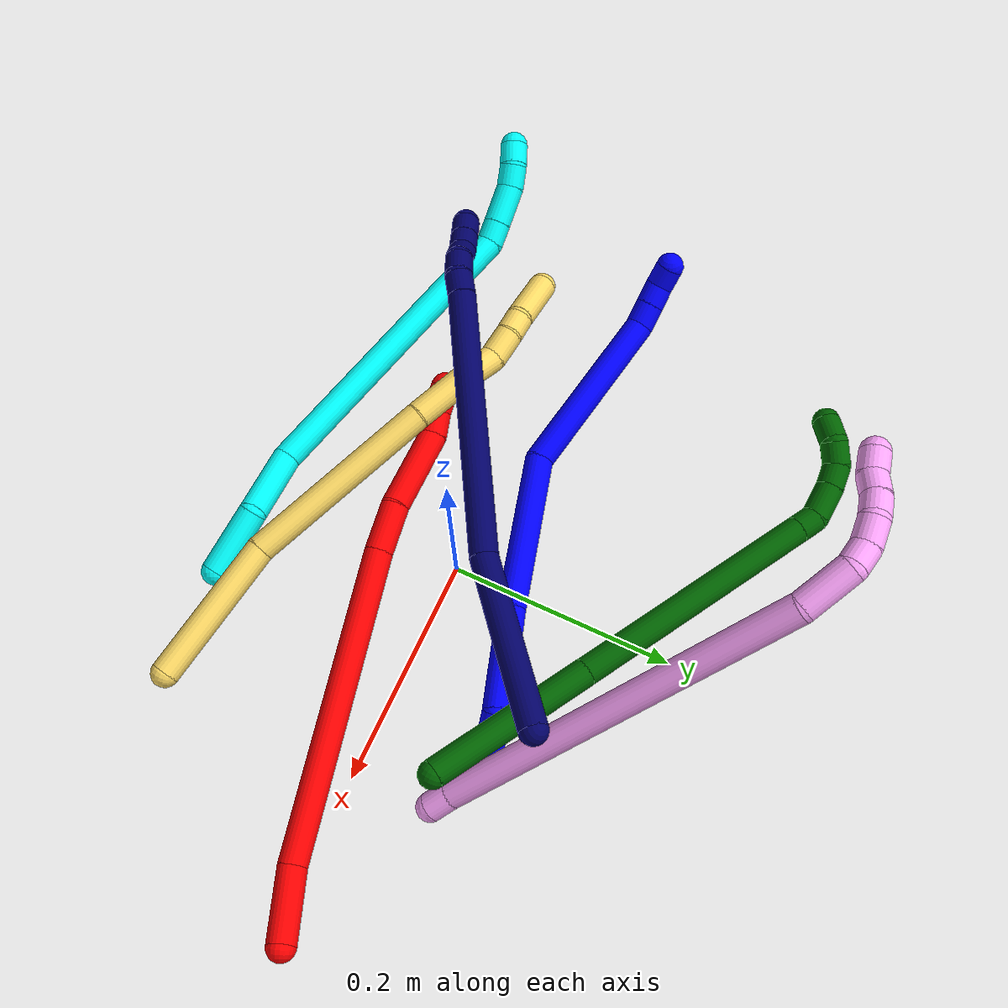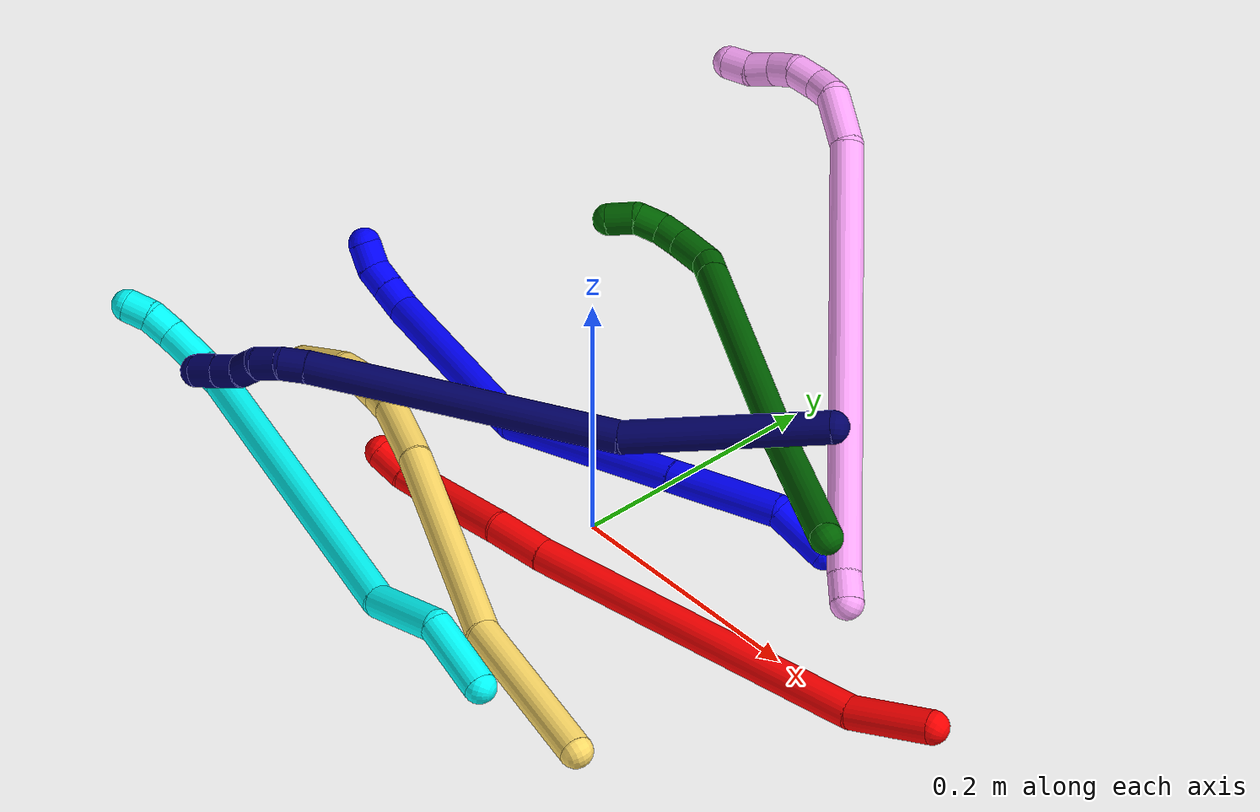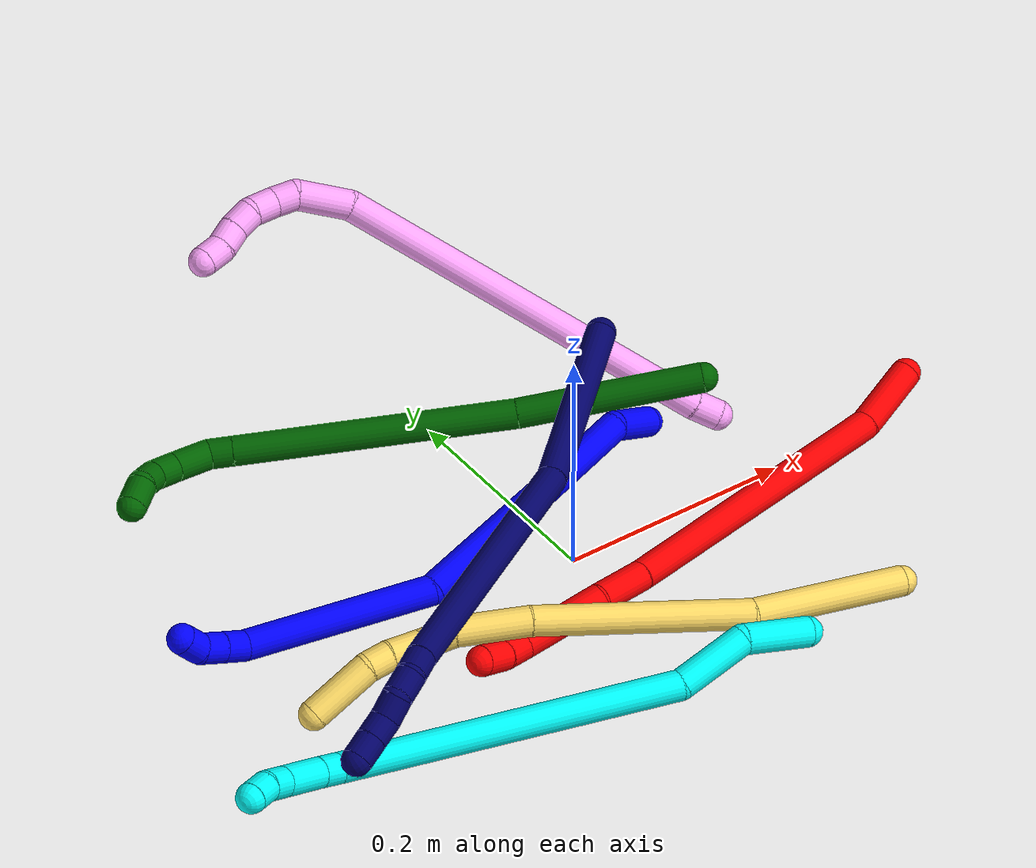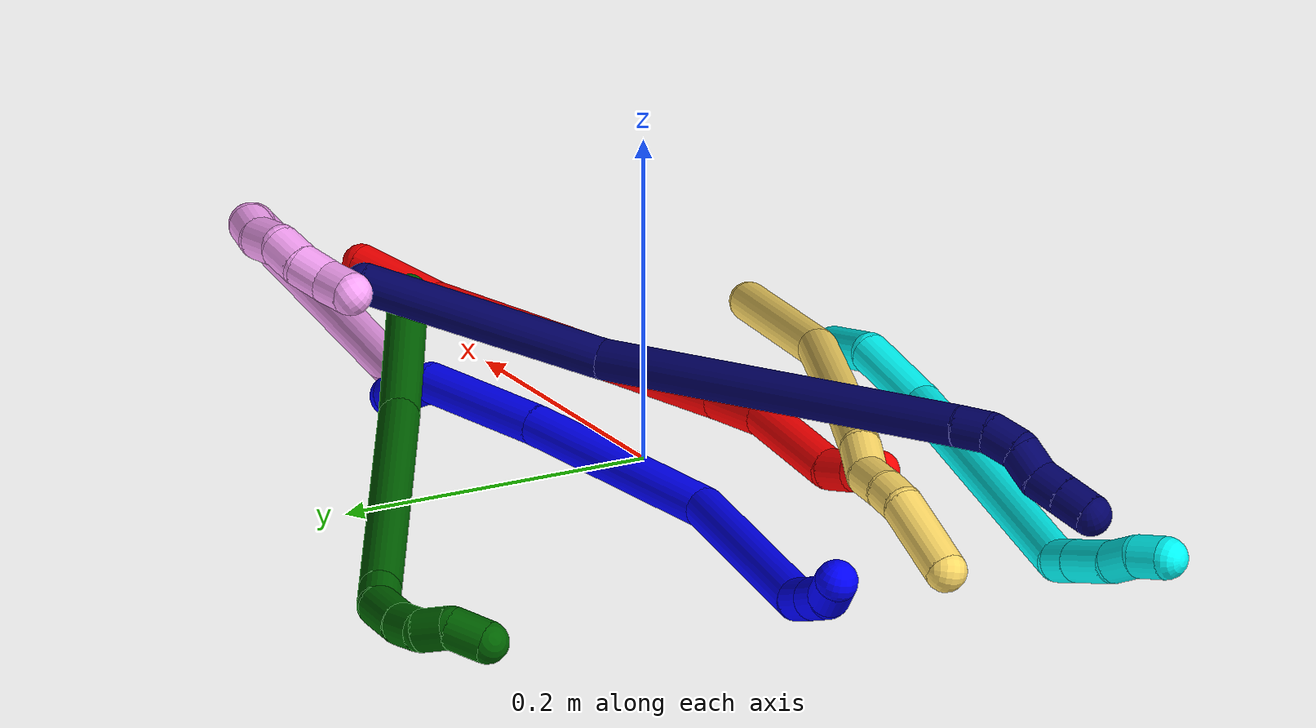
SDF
<sdf version="1.7">
 <world name="default">
  <plugin name="TubeGeneratorPlugin" filename="libtube_generator_plugin.so"/>
  <model name="photoneo_s_sensor">
   <static>1</static>
   <pose>0 0 2 1.57079 1.57079 3.14159</pose>
   <link name="link">
    <inertial><mass>0.1</mass></inertial>
    <sensor name="sensor" type="depth">
     <update_rate>30</update_rate>
     <camera>
      <horizontal_fov>1.22</horizontal_fov>
      <image><width>1920</width><height>1200</height><format>B8G8R8</format></image>
      <clip><near>0.1</near><far>4</far></clip>
      <depth_camera><output>points</output></depth_camera>
     </camera>
     <plugin name="camera_plugin" filename="libgazebo_ros_depth_camera.so">
      <baseline>0.2</baseline>
      <alwaysOn>1</alwaysOn>
      <updateRate>0.0</updateRate>
      <cameraName>camera_ir</cameraName>
      <imageTopicName>/camera/color/image_raw</imageTopicName>
      <cameraInfoTopicName>/camera/color/camera_info</cameraInfoTopicName>
      <depthImageTopicName>/camera/depth/image_raw</depthImageTopicName>
      <depthImageCameraInfoTopicName>/camera/depth/camera_info</depthImageCameraInfoTopicName>
      <pointCloudTopicName>/camera/depth/points</pointCloudTopicName>
      <frameName>fr_optical</frameName>
      <pointCloudCutoff>0.1</pointCloudCutoff>
      <pointCloudCutoffMax>2.0</pointCloudCutoffMax>
      <distortionK1>0</distortionK1>
      <distortionK2>0</distortionK2>
      <distortionK3>0</distortionK3>
      <distortionT1>0</distortionT1>
      <distortionT2>0</distortionT2>
      <CxPrime>0</CxPrime>
      <Cx>0</Cx>
      <Cy>0</Cy>
      <focalLength>0</focalLength>
      <hackBaseline>0</hackBaseline>
     </plugin>
    </sensor>
   </link>
  </model>
  <gravity>0 0 -9.8</gravity>
  <magnetic_field>6e-06 2.3e-05 -4.2e-05</magnetic_field>
  <atmosphere type="adiabatic"/>
  <physics name="default_physics" default="0" type="ode">
   <max_step_size>0.003</max_step_size>
   <real_time_factor>1</real_time_factor>
   <real_time_update_rate>1000</real_time_update_rate>
   <max_contacts>10000</max_contacts>
   <ode>
    <solver>
     <type>quick</type>
     <iters>100</iters>
     <sor>1.3</sor>
     <use_dynamic_moi_rescaling>0</use_dynamic_moi_rescaling>
    </solver>
    <constraints>
     <contact_max_correcting_vel>0</contact_max_correcting_vel>
     <contact_surface_layer>0.001</contact_surface_layer>
     <cfm>0</cfm>
     <erp>0.2</erp>
    </constraints>
   </ode>
  </physics>
  <scene><ambient>0.4 0.4 0.4 1</ambient><background>0.7 0.7 0.7 1</background><shadows>0</shadows></scene>
  <audio><device>default</device></audio>
  <spherical_coordinates>
   <surface_model>EARTH_WGS84</surface_model>
   <latitude_deg>0</latitude_deg>
   <longitude_deg>0</longitude_deg>
   <elevation>0</elevation>
   <heading_deg>0</heading_deg>
  </spherical_coordinates>
  <model name="bin">
   <static>1</static>
   <link name="bottom">
    <collision name="collision-bottom">
     <pose>0 0 -0.01 0 -0 0</pose>
     <geometry><box><size>0.8 0.6 0.02</size></box></geometry>
     <surface>
      <friction><ode><mu>100</mu><mu2>100</mu2></ode></friction>
      <contact><collide_bitmask>65535</collide_bitmask></contact>
     </surface>
    </collision>
   </link>
   <link name="west_wall">
    <collision name="collision-west_wall">
     <pose>-0.41 0 0.1 0 -0 0</pose>
     <geometry><box><size>0.02 0.6 0.2</size></box></geometry>
     <surface>
      <friction><ode><mu>100</mu><mu2>100</mu2></ode></friction>
      <contact><collide_bitmask>65535</collide_bitmask></contact>
     </surface>
    </collision>
   </link>
   <link name="east_wall">
    <collision name="collision-east_wall">
     <pose>0.41 0 0.1 0 -0 0</pose>
     <geometry><box><size>0.02 0.6 0.2</size></box></geometry>
     <surface>
      <friction><ode><mu>100</mu><mu2>100</mu2></ode></friction>
      <contact><collide_bitmask>65535</collide_bitmask></contact>
     </surface>
    </collision>
   </link>
   <link name="south_wall">
    <collision name="collision-south_wall">
     <pose>0 -0.31 0.1 0 -0 0</pose>
     <geometry><box><size>0.8 0.02 0.2</size></box></geometry>
     <surface>
      <friction><ode><mu>100</mu><mu2>100</mu2></ode></friction>
      <contact><collide_bitmask>65535</collide_bitmask></contact>
     </surface>
    </collision>
   </link>
   <link name="north_wall">
    <collision name="collision-north_wall">
     <pose>0 0.31 0.1 0 -0 0</pose>
     <geometry><box><size>0.8 0.02 0.2</size></box></geometry>
     <surface>
      <friction><ode><mu>100</mu><mu2>100</mu2></ode></friction>
      <contact><collide_bitmask>65535</collide_bitmask></contact>
     </surface>
    </collision>
   </link>
  </model>
  <model name="1">
   <static>0</static>
   <link name="1">
    <collision name="collision-cylinder-e_1_1_4">
     <pose>-0.016124 -0.003632 0.014654 0.242979 -0.818259 -0.105777</pose>
     <geometry><cylinder><radius>0.0125</radius><length>0.044178</length></cylinder></geometry>
     <surface>
      <friction><ode><mu>1.16</mu><mu2>1.16</mu2><slip1>0</slip1><slip2>0</slip2></ode></friction>
      <contact><ode><kp>1e+06</kp><kd>1</kd><max_vel>0</max_vel><min_depth>0.001</min_depth></ode></contact>
     </surface>
    </collision>
    <visual name="visual-cylinder-e_1_1_4">
     <pose>-0.016124 -0.003632 0.014654 0.242979 -0.818259 -0.105777</pose>
     <geometry><cylinder><radius>0.0125</radius><length>0.044178</length></cylinder></geometry>
     <material><ambient>0 0 1 1</ambient></material>
    </visual>
    <collision name="collision-cylinder-e_2_4_5">
     <pose>-0.072965 -0.022601 0.039042 1.00528 -1.15118 -0.685292</pose>
     <geometry><cylinder><radius>0.0125</radius><length>0.08917</length></cylinder></geometry>
     <surface>
      <friction><ode><mu>1.16</mu><mu2>1.16</mu2><slip1>0</slip1><slip2>0</slip2></ode></friction>
      <contact><ode><kp>1e+06</kp><kd>1</kd><max_vel>0</max_vel><min_depth>0.001</min_depth></ode></contact>
     </surface>
    </collision>
    <visual name="visual-cylinder-e_2_4_5">
     <pose>-0.072965 -0.022601 0.039042 1.00528 -1.15118 -0.685292</pose>
     <geometry><cylinder><radius>0.0125</radius><length>0.08917</length></cylinder></geometry>
     <material><ambient>0 0 1 1</ambient></material>
    </visual>
    <collision name="collision-cylinder-e_3_5_6">
     <pose>-0.180783 -0.060097 0.061706 1.04257 -1.2056 -0.752795</pose>
     <geometry><cylinder><radius>0.0125</radius><length>0.143676</length></cylinder></geometry>
     <surface>
      <friction><ode><mu>1.16</mu><mu2>1.16</mu2><slip1>0</slip1><slip2>0</slip2></ode></friction>
      <contact><ode><kp>1e+06</kp><kd>1</kd><max_vel>0</max_vel><min_depth>0.001</min_depth></ode></contact>
     </surface>
    </collision>
    <visual name="visual-cylinder-e_3_5_6">
     <pose>-0.180783 -0.060097 0.061706 1.04257 -1.2056 -0.752795</pose>
     <geometry><cylinder><radius>0.0125</radius><length>0.143676</length></cylinder></geometry>
     <material><ambient>0 0 1 1</ambient></material>
    </visual>
    <collision name="collision-cylinder-e_4_6_7">
     <pose>-0.325239 -0.071338 0.093514 -0.524346 -1.29601 0.40086</pose>
     <geometry><cylinder><radius>0.0125</radius><length>0.160742</length></cylinder></geometry>
     <surface>
      <friction><ode><mu>1.16</mu><mu2>1.16</mu2><slip1>0</slip1><slip2>0</slip2></ode></friction>
      <contact><ode><kp>1e+06</kp><kd>1</kd><max_vel>0</max_vel><min_depth>0.001</min_depth></ode></contact>
     </surface>
    </collision>
    <visual name="visual-cylinder-e_4_6_7">
     <pose>-0.325239 -0.071338 0.093514 -0.524346 -1.29601 0.40086</pose>
     <geometry><cylinder><radius>0.0125</radius><length>0.160742</length></cylinder></geometry>
     <material><ambient>0 0 1 1</ambient></material>
    </visual>
    <collision name="collision-cylinder-e_5_7_8">
     <pose>-0.411463 -0.059776 0.118504 -0.104934 -0.964769 0.054985</pose>
     <geometry><cylinder><radius>0.0125</radius><length>0.021578</length></cylinder></geometry>
     <surface>
      <friction><ode><mu>1.16</mu><mu2>1.16</mu2><slip1>0</slip1><slip2>0</slip2></ode></friction>
      <contact><ode><kp>1e+06</kp><kd>1</kd><max_vel>0</max_vel><min_depth>0.001</min_depth></ode></contact>
     </surface>
    </collision>
    <visual name="visual-cylinder-e_5_7_8">
     <pose>-0.411463 -0.059776 0.118504 -0.104934 -0.964769 0.054985</pose>
     <geometry><cylinder><radius>0.0125</radius><length>0.021578</length></cylinder></geometry>
     <material><ambient>0 0 1 1</ambient></material>
    </visual>
    <collision name="collision-cylinder-e_6_8_9">
     <pose>-0.428602 -0.058556 0.130461 -0.098242 -0.9533 0.050758</pose>
     <geometry><cylinder><radius>0.0125</radius><length>0.02029</length></cylinder></geometry>
     <surface>
      <friction><ode><mu>1.16</mu><mu2>1.16</mu2><slip1>0</slip1><slip2>0</slip2></ode></friction>
      <contact><ode><kp>1e+06</kp><kd>1</kd><max_vel>0</max_vel><min_depth>0.001</min_depth></ode></contact>
     </surface>
    </collision>
    <visual name="visual-cylinder-e_6_8_9">
     <pose>-0.428602 -0.058556 0.130461 -0.098242 -0.9533 0.050758</pose>
     <geometry><cylinder><radius>0.0125</radius><length>0.02029</length></cylinder></geometry>
     <material><ambient>0 0 1 1</ambient></material>
    </visual>
    <collision name="collision-cylinder-e_7_9_2">
     <pose>-0.441809 -0.055817 0.144947 -0.245351 -0.506044 0.063737</pose>
     <geometry><cylinder><radius>0.0125</radius><length>0.020366</length></cylinder></geometry>
     <surface>
      <friction><ode><mu>1.16</mu><mu2>1.16</mu2><slip1>0</slip1><slip2>0</slip2></ode></friction>
      <contact><ode><kp>1e+06</kp><kd>1</kd><max_vel>0</max_vel><min_depth>0.001</min_depth></ode></contact>
     </surface>
    </collision>
    <visual name="visual-cylinder-e_7_9_2">
     <pose>-0.441809 -0.055817 0.144947 -0.245351 -0.506044 0.063737</pose>
     <geometry><cylinder><radius>0.0125</radius><length>0.020366</length></cylinder></geometry>
     <material><ambient>0 0 1 1</ambient></material>
    </visual>
    <collision name="collision-sphere-2">
     <pose>-0.446745 -0.053653 0.153587 0 -0 0</pose>
     <geometry><sphere><radius>0.0125</radius></sphere></geometry>
     <surface>
      <friction><ode><mu>1.16</mu><mu2>1.16</mu2><slip1>0</slip1><slip2>0</slip2></ode></friction>
      <contact><ode><kp>1e+06</kp><kd>1</kd><max_vel>0</max_vel><min_depth>0.001</min_depth></ode></contact>
     </surface>
    </collision>
    <visual name="visual-sphere-2">
     <pose>-0.446745 -0.053653 0.153587 0 -0 0</pose>
     <geometry><sphere><radius>0.0125</radius></sphere></geometry>
     <material><ambient>0 0 1 1</ambient></material>
    </visual>
    <collision name="collision-sphere-9">
     <pose>-0.436873 -0.05798 0.136307 0 -0 0</pose>
     <geometry><sphere><radius>0.0125</radius></sphere></geometry>
     <surface>
      <friction><ode><mu>1.16</mu><mu2>1.16</mu2><slip1>0</slip1><slip2>0</slip2></ode></friction>
      <contact><ode><kp>1e+06</kp><kd>1</kd><max_vel>0</max_vel><min_depth>0.001</min_depth></ode></contact>
     </surface>
    </collision>
    <visual name="visual-sphere-9">
     <pose>-0.436873 -0.05798 0.136307 0 -0 0</pose>
     <geometry><sphere><radius>0.0125</radius></sphere></geometry>
     <material><ambient>0 0 1 1</ambient></material>
    </visual>
    <collision name="collision-sphere-4">
     <pose>-0.032248 -0.007265 0.029308 0 -0 0</pose>
     <geometry><sphere><radius>0.0125</radius></sphere></geometry>
     <surface>
      <friction><ode><mu>1.16</mu><mu2>1.16</mu2><slip1>0</slip1><slip2>0</slip2></ode></friction>
      <contact><ode><kp>1e+06</kp><kd>1</kd><max_vel>0</max_vel><min_depth>0.001</min_depth></ode></contact>
     </surface>
    </collision>
    <visual name="visual-sphere-4">
     <pose>-0.032248 -0.007265 0.029308 0 -0 0</pose>
     <geometry><sphere><radius>0.0125</radius></sphere></geometry>
     <material><ambient>0 0 1 1</ambient></material>
    </visual>
    <collision name="collision-sphere-1">
     <geometry><sphere><radius>0.0125</radius></sphere></geometry>
     <surface>
      <friction><ode><mu>1.16</mu><mu2>1.16</mu2><slip1>0</slip1><slip2>0</slip2></ode></friction>
      <contact><ode><kp>1e+06</kp><kd>1</kd><max_vel>0</max_vel><min_depth>0.001</min_depth></ode></contact>
     </surface>
    </collision>
    <visual name="visual-sphere-1">
     <geometry><sphere><radius>0.0125</radius></sphere></geometry>
     <material><ambient>0 0 1 1</ambient></material>
    </visual>
    <collision name="collision-sphere-8">
     <pose>-0.42033 -0.059132 0.124616 0 -0 0</pose>
     <geometry><sphere><radius>0.0125</radius></sphere></geometry>
     <surface>
      <friction><ode><mu>1.16</mu><mu2>1.16</mu2><slip1>0</slip1><slip2>0</slip2></ode></friction>
      <contact><ode><kp>1e+06</kp><kd>1</kd><max_vel>0</max_vel><min_depth>0.001</min_depth></ode></contact>
     </surface>
    </collision>
    <visual name="visual-sphere-8">
     <pose>-0.42033 -0.059132 0.124616 0 -0 0</pose>
     <geometry><sphere><radius>0.0125</radius></sphere></geometry>
     <material><ambient>0 0 1 1</ambient></material>
    </visual>
    <collision name="collision-sphere-5">
     <pose>-0.113682 -0.037938 0.048775 0 -0 0</pose>
     <geometry><sphere><radius>0.0125</radius></sphere></geometry>
     <surface>
      <friction><ode><mu>1.16</mu><mu2>1.16</mu2><slip1>0</slip1><slip2>0</slip2></ode></friction>
      <contact><ode><kp>1e+06</kp><kd>1</kd><max_vel>0</max_vel><min_depth>0.001</min_depth></ode></contact>
     </surface>
    </collision>
    <visual name="visual-sphere-5">
     <pose>-0.113682 -0.037938 0.048775 0 -0 0</pose>
     <geometry><sphere><radius>0.0125</radius></sphere></geometry>
     <material><ambient>0 0 1 1</ambient></material>
    </visual>
    <collision name="collision-sphere-6">
     <pose>-0.247883 -0.082256 0.074636 0 -0 0</pose>
     <geometry><sphere><radius>0.0125</radius></sphere></geometry>
     <surface>
      <friction><ode><mu>1.16</mu><mu2>1.16</mu2><slip1>0</slip1><slip2>0</slip2></ode></friction>
      <contact><ode><kp>1e+06</kp><kd>1</kd><max_vel>0</max_vel><min_depth>0.001</min_depth></ode></contact>
     </surface>
    </collision>
    <visual name="visual-sphere-6">
     <pose>-0.247883 -0.082256 0.074636 0 -0 0</pose>
     <geometry><sphere><radius>0.0125</radius></sphere></geometry>
     <material><ambient>0 0 1 1</ambient></material>
    </visual>
    <collision name="collision-sphere-7">
     <pose>-0.402595 -0.06042 0.112392 0 -0 0</pose>
     <geometry><sphere><radius>0.0125</radius></sphere></geometry>
     <surface>
      <friction><ode><mu>1.16</mu><mu2>1.16</mu2><slip1>0</slip1><slip2>0</slip2></ode></friction>
      <contact><ode><kp>1e+06</kp><kd>1</kd><max_vel>0</max_vel><min_depth>0.001</min_depth></ode></contact>
     </surface>
    </collision>
    <visual name="visual-sphere-7">
     <pose>-0.402595 -0.06042 0.112392 0 -0 0</pose>
     <geometry><sphere><radius>0.0125</radius></sphere></geometry>
     <material><ambient>0 0 1 1</ambient></material>
    </visual>
    <inertial>
     <pose>-0.22409 -0.051784 0.072364 0 -0 0</pose>
     <mass>0.5</mass>
     <inertia>
      <ixx>0.000107</ixx>
      <ixy>0</ixy>
      <ixz>0</ixz>
      <iyy>0.000604</iyy>
      <iyz>0</iyz>
      <izz>0.000707</izz>
     </inertia>
    </inertial>
   </link>
   <pose>0.142989 0.096451 0.011498 0.133901 -0.248833 -0.076624</pose>
  </model>
  <model name="2">
   <static>0</static>
   <link name="2">
    <collision name="collision-cylinder-e_1_1_4">
     <pose>-0.010847 0.006863 -0.028928 -2.90867 -0.349832 1.97205</pose>
     <geometry><cylinder><radius>0.0125</radius><length>0.063295</length></cylinder></geometry>
     <surface>
      <friction><ode><mu>1.16</mu><mu2>1.16</mu2><slip1>0</slip1><slip2>0</slip2></ode></friction>
      <contact><ode><kp>1e+06</kp><kd>1</kd><max_vel>0</max_vel><min_depth>0.001</min_depth></ode></contact>
     </surface>
    </collision>
    <visual name="visual-cylinder-e_1_1_4">
     <pose>-0.010847 0.006863 -0.028928 -2.90867 -0.349832 1.97205</pose>
     <geometry><cylinder><radius>0.0125</radius><length>0.063295</length></cylinder></geometry>
     <material><ambient>1 0 0 1</ambient></material>
    </visual>
    <collision name="collision-cylinder-e_2_4_5">
     <pose>-0.054925 0.010246 -0.188528 3.11497 -0.248945 -2.92964</pose>
     <geometry><cylinder><radius>0.0125</radius><length>0.269755</length></cylinder></geometry>
     <surface>
      <friction><ode><mu>1.16</mu><mu2>1.16</mu2><slip1>0</slip1><slip2>0</slip2></ode></friction>
      <contact><ode><kp>1e+06</kp><kd>1</kd><max_vel>0</max_vel><min_depth>0.001</min_depth></ode></contact>
     </surface>
    </collision>
    <visual name="visual-cylinder-e_2_4_5">
     <pose>-0.054925 0.010246 -0.188528 3.11497 -0.248945 -2.92964</pose>
     <geometry><cylinder><radius>0.0125</radius><length>0.269755</length></cylinder></geometry>
     <material><ambient>1 0 0 1</ambient></material>
    </visual>
    <collision name="collision-cylinder-e_3_5_6">
     <pose>-0.094009 0.004577 -0.340396 3.03862 -0.268089 -2.41155</pose>
     <geometry><cylinder><radius>0.0125</radius><length>0.044193</length></cylinder></geometry>
     <surface>
      <friction><ode><mu>1.16</mu><mu2>1.16</mu2><slip1>0</slip1><slip2>0</slip2></ode></friction>
      <contact><ode><kp>1e+06</kp><kd>1</kd><max_vel>0</max_vel><min_depth>0.001</min_depth></ode></contact>
     </surface>
    </collision>
    <visual name="visual-cylinder-e_3_5_6">
     <pose>-0.094009 0.004577 -0.340396 3.03862 -0.268089 -2.41155</pose>
     <geometry><cylinder><radius>0.0125</radius><length>0.044193</length></cylinder></geometry>
     <material><ambient>1 0 0 1</ambient></material>
    </visual>
    <collision name="collision-cylinder-e_4_6_7">
     <pose>-0.117105 -0.002173 -0.395254 3.00696 -0.469691 -2.59228</pose>
     <geometry><cylinder><radius>0.0125</radius><length>0.076193</length></cylinder></geometry>
     <surface>
      <friction><ode><mu>1.16</mu><mu2>1.16</mu2><slip1>0</slip1><slip2>0</slip2></ode></friction>
      <contact><ode><kp>1e+06</kp><kd>1</kd><max_vel>0</max_vel><min_depth>0.001</min_depth></ode></contact>
     </surface>
    </collision>
    <visual name="visual-cylinder-e_4_6_7">
     <pose>-0.117105 -0.002173 -0.395254 3.00696 -0.469691 -2.59228</pose>
     <geometry><cylinder><radius>0.0125</radius><length>0.076193</length></cylinder></geometry>
     <material><ambient>1 0 0 1</ambient></material>
    </visual>
    <collision name="collision-cylinder-e_5_7_8">
     <pose>-0.135219 -0.007335 -0.440179 3.08821 -0.077015 -1.92954</pose>
     <geometry><cylinder><radius>0.0125</radius><length>0.022622</length></cylinder></geometry>
     <surface>
      <friction><ode><mu>1.16</mu><mu2>1.16</mu2><slip1>0</slip1><slip2>0</slip2></ode></friction>
      <contact><ode><kp>1e+06</kp><kd>1</kd><max_vel>0</max_vel><min_depth>0.001</min_depth></ode></contact>
     </surface>
    </collision>
    <visual name="visual-cylinder-e_5_7_8">
     <pose>-0.135219 -0.007335 -0.440179 3.08821 -0.077015 -1.92954</pose>
     <geometry><cylinder><radius>0.0125</radius><length>0.022622</length></cylinder></geometry>
     <material><ambient>1 0 0 1</ambient></material>
    </visual>
    <collision name="collision-cylinder-e_6_8_2">
     <pose>-0.136548 -0.010688 -0.463082 2.90951 -0.038347 -0.326091</pose>
     <geometry><cylinder><radius>0.0125</radius><length>0.023942</length></cylinder></geometry>
     <surface>
      <friction><ode><mu>1.16</mu><mu2>1.16</mu2><slip1>0</slip1><slip2>0</slip2></ode></friction>
      <contact><ode><kp>1e+06</kp><kd>1</kd><max_vel>0</max_vel><min_depth>0.001</min_depth></ode></contact>
     </surface>
    </collision>
    <visual name="visual-cylinder-e_6_8_2">
     <pose>-0.136548 -0.010688 -0.463082 2.90951 -0.038347 -0.326091</pose>
     <geometry><cylinder><radius>0.0125</radius><length>0.023942</length></cylinder></geometry>
     <material><ambient>1 0 0 1</ambient></material>
    </visual>
    <collision name="collision-sphere-2">
     <pose>-0.137007 -0.013439 -0.474724 0 -0 0</pose>
     <geometry><sphere><radius>0.0125</radius></sphere></geometry>
     <surface>
      <friction><ode><mu>1.16</mu><mu2>1.16</mu2><slip1>0</slip1><slip2>0</slip2></ode></friction>
      <contact><ode><kp>1e+06</kp><kd>1</kd><max_vel>0</max_vel><min_depth>0.001</min_depth></ode></contact>
     </surface>
    </collision>
    <visual name="visual-sphere-2">
     <pose>-0.137007 -0.013439 -0.474724 0 -0 0</pose>
     <geometry><sphere><radius>0.0125</radius></sphere></geometry>
     <material><ambient>1 0 0 1</ambient></material>
    </visual>
    <collision name="collision-sphere-4">
     <pose>-0.021694 0.013725 -0.057855 0 -0 0</pose>
     <geometry><sphere><radius>0.0125</radius></sphere></geometry>
     <surface>
      <friction><ode><mu>1.16</mu><mu2>1.16</mu2><slip1>0</slip1><slip2>0</slip2></ode></friction>
      <contact><ode><kp>1e+06</kp><kd>1</kd><max_vel>0</max_vel><min_depth>0.001</min_depth></ode></contact>
     </surface>
    </collision>
    <visual name="visual-sphere-4">
     <pose>-0.021694 0.013725 -0.057855 0 -0 0</pose>
     <geometry><sphere><radius>0.0125</radius></sphere></geometry>
     <material><ambient>1 0 0 1</ambient></material>
    </visual>
    <collision name="collision-sphere-1">
     <geometry><sphere><radius>0.0125</radius></sphere></geometry>
     <surface>
      <friction><ode><mu>1.16</mu><mu2>1.16</mu2><slip1>0</slip1><slip2>0</slip2></ode></friction>
      <contact><ode><kp>1e+06</kp><kd>1</kd><max_vel>0</max_vel><min_depth>0.001</min_depth></ode></contact>
     </surface>
    </collision>
    <visual name="visual-sphere-1">
     <geometry><sphere><radius>0.0125</radius></sphere></geometry>
     <material><ambient>1 0 0 1</ambient></material>
    </visual>
    <collision name="collision-sphere-8">
     <pose>-0.136089 -0.007937 -0.451441 0 -0 0</pose>
     <geometry><sphere><radius>0.0125</radius></sphere></geometry>
     <surface>
      <friction><ode><mu>1.16</mu><mu2>1.16</mu2><slip1>0</slip1><slip2>0</slip2></ode></friction>
      <contact><ode><kp>1e+06</kp><kd>1</kd><max_vel>0</max_vel><min_depth>0.001</min_depth></ode></contact>
     </surface>
    </collision>
    <visual name="visual-sphere-8">
     <pose>-0.136089 -0.007937 -0.451441 0 -0 0</pose>
     <geometry><sphere><radius>0.0125</radius></sphere></geometry>
     <material><ambient>1 0 0 1</ambient></material>
    </visual>
    <collision name="collision-sphere-5">
     <pose>-0.088156 0.006767 -0.319202 0 -0 0</pose>
     <geometry><sphere><radius>0.0125</radius></sphere></geometry>
     <surface>
      <friction><ode><mu>1.16</mu><mu2>1.16</mu2><slip1>0</slip1><slip2>0</slip2></ode></friction>
      <contact><ode><kp>1e+06</kp><kd>1</kd><max_vel>0</max_vel><min_depth>0.001</min_depth></ode></contact>
     </surface>
    </collision>
    <visual name="visual-sphere-5">
     <pose>-0.088156 0.006767 -0.319202 0 -0 0</pose>
     <geometry><sphere><radius>0.0125</radius></sphere></geometry>
     <material><ambient>1 0 0 1</ambient></material>
    </visual>
    <collision name="collision-sphere-6">
     <pose>-0.099863 0.002386 -0.36159 0 -0 0</pose>
     <geometry><sphere><radius>0.0125</radius></sphere></geometry>
     <surface>
      <friction><ode><mu>1.16</mu><mu2>1.16</mu2><slip1>0</slip1><slip2>0</slip2></ode></friction>
      <contact><ode><kp>1e+06</kp><kd>1</kd><max_vel>0</max_vel><min_depth>0.001</min_depth></ode></contact>
     </surface>
    </collision>
    <visual name="visual-sphere-6">
     <pose>-0.099863 0.002386 -0.36159 0 -0 0</pose>
     <geometry><sphere><radius>0.0125</radius></sphere></geometry>
     <material><ambient>1 0 0 1</ambient></material>
    </visual>
    <collision name="collision-sphere-7">
     <pose>-0.134348 -0.006733 -0.428918 0 -0 0</pose>
     <geometry><sphere><radius>0.0125</radius></sphere></geometry>
     <surface>
      <friction><ode><mu>1.16</mu><mu2>1.16</mu2><slip1>0</slip1><slip2>0</slip2></ode></friction>
      <contact><ode><kp>1e+06</kp><kd>1</kd><max_vel>0</max_vel><min_depth>0.001</min_depth></ode></contact>
     </surface>
    </collision>
    <visual name="visual-sphere-7">
     <pose>-0.134348 -0.006733 -0.428918 0 -0 0</pose>
     <geometry><sphere><radius>0.0125</radius></sphere></geometry>
     <material><ambient>1 0 0 1</ambient></material>
    </visual>
    <inertial>
     <pose>-0.069816 0.005626 -0.237782 0 -0 0</pose>
     <mass>0.5</mass>
     <inertia>
      <ixx>-0.001957</ixx>
      <ixy>0</ixy>
      <ixz>0</ixz>
      <iyy>0.001319</iyy>
      <iyz>0</iyz>
      <izz>0.000441</izz>
     </inertia>
    </inertial>
   </link>
   <pose>0.342022 0.01339 0.023901 -2.02963 -1.01857 -0.82615</pose>
  </model>
  <model name="3">
   <static>0</static>
   <link name="3">
    <collision name="collision-cylinder-e_1_1_4">
     <pose>-0.00683 0.013975 0.025654 -0.498806 -0.229664 0.058738</pose>
     <geometry><cylinder><radius>0.0125</radius><length>0.060003</length></cylinder></geometry>
     <surface>
      <friction><ode><mu>1.16</mu><mu2>1.16</mu2><slip1>0</slip1><slip2>0</slip2></ode></friction>
      <contact><ode><kp>1e+06</kp><kd>1</kd><max_vel>0</max_vel><min_depth>0.001</min_depth></ode></contact>
     </surface>
    </collision>
    <visual name="visual-cylinder-e_1_1_4">
     <pose>-0.00683 0.013975 0.025654 -0.498806 -0.229664 0.058738</pose>
     <geometry><cylinder><radius>0.0125</radius><length>0.060003</length></cylinder></geometry>
     <material><ambient>0.003922 1 0.996078 1</ambient></material>
    </visual>
    <collision name="collision-cylinder-e_2_4_5">
     <pose>-0.028124 0.028269 0.079014 -0.011512 -0.48111 0.002824</pose>
     <geometry><cylinder><radius>0.0125</radius><length>0.062512</length></cylinder></geometry>
     <surface>
      <friction><ode><mu>1.16</mu><mu2>1.16</mu2><slip1>0</slip1><slip2>0</slip2></ode></friction>
      <contact><ode><kp>1e+06</kp><kd>1</kd><max_vel>0</max_vel><min_depth>0.001</min_depth></ode></contact>
     </surface>
    </collision>
    <visual name="visual-cylinder-e_2_4_5">
     <pose>-0.028124 0.028269 0.079014 -0.011512 -0.48111 0.002824</pose>
     <geometry><cylinder><radius>0.0125</radius><length>0.062512</length></cylinder></geometry>
     <material><ambient>0.003922 1 0.996078 1</ambient></material>
    </visual>
    <collision name="collision-cylinder-e_3_5_6">
     <pose>-0.10916 0.081445 0.218378 -0.442126 -0.494267 0.113276</pose>
     <geometry><cylinder><radius>0.0125</radius><length>0.280665</length></cylinder></geometry>
     <surface>
      <friction><ode><mu>1.16</mu><mu2>1.16</mu2><slip1>0</slip1><slip2>0</slip2></ode></friction>
      <contact><ode><kp>1e+06</kp><kd>1</kd><max_vel>0</max_vel><min_depth>0.001</min_depth></ode></contact>
     </surface>
    </collision>
    <visual name="visual-cylinder-e_3_5_6">
     <pose>-0.10916 0.081445 0.218378 -0.442126 -0.494267 0.113276</pose>
     <geometry><cylinder><radius>0.0125</radius><length>0.280665</length></cylinder></geometry>
     <material><ambient>0.003922 1 0.996078 1</ambient></material>
    </visual>
    <collision name="collision-cylinder-e_4_6_7">
     <pose>-0.176403 0.138046 0.339335 -0.382797 -0.066891 0.012966</pose>
     <geometry><cylinder><radius>0.0125</radius><length>0.020093</length></cylinder></geometry>
     <surface>
      <friction><ode><mu>1.16</mu><mu2>1.16</mu2><slip1>0</slip1><slip2>0</slip2></ode></friction>
      <contact><ode><kp>1e+06</kp><kd>1</kd><max_vel>0</max_vel><min_depth>0.001</min_depth></ode></contact>
     </surface>
    </collision>
    <visual name="visual-cylinder-e_4_6_7">
     <pose>-0.176403 0.138046 0.339335 -0.382797 -0.066891 0.012966</pose>
     <geometry><cylinder><radius>0.0125</radius><length>0.020093</length></cylinder></geometry>
     <material><ambient>0.003922 1 0.996078 1</ambient></material>
    </visual>
    <collision name="collision-cylinder-e_5_7_8">
     <pose>-0.178321 0.148102 0.365366 -0.360744 -0.069574 0.012692</pose>
     <geometry><cylinder><radius>0.0125</radius><length>0.035853</length></cylinder></geometry>
     <surface>
      <friction><ode><mu>1.16</mu><mu2>1.16</mu2><slip1>0</slip1><slip2>0</slip2></ode></friction>
      <contact><ode><kp>1e+06</kp><kd>1</kd><max_vel>0</max_vel><min_depth>0.001</min_depth></ode></contact>
     </surface>
    </collision>
    <visual name="visual-cylinder-e_5_7_8">
     <pose>-0.178321 0.148102 0.365366 -0.360744 -0.069574 0.012692</pose>
     <geometry><cylinder><radius>0.0125</radius><length>0.035853</length></cylinder></geometry>
     <material><ambient>0.003922 1 0.996078 1</ambient></material>
    </visual>
    <collision name="collision-cylinder-e_6_8_9">
     <pose>-0.17794 0.157694 0.391823 -0.325249 0.157182 -0.025841</pose>
     <geometry><cylinder><radius>0.0125</radius><length>0.020782</length></cylinder></geometry>
     <surface>
      <friction><ode><mu>1.16</mu><mu2>1.16</mu2><slip1>0</slip1><slip2>0</slip2></ode></friction>
      <contact><ode><kp>1e+06</kp><kd>1</kd><max_vel>0</max_vel><min_depth>0.001</min_depth></ode></contact>
     </surface>
    </collision>
    <visual name="visual-cylinder-e_6_8_9">
     <pose>-0.17794 0.157694 0.391823 -0.325249 0.157182 -0.025841</pose>
     <geometry><cylinder><radius>0.0125</radius><length>0.020782</length></cylinder></geometry>
     <material><ambient>0.003922 1 0.996078 1</ambient></material>
    </visual>
    <collision name="collision-cylinder-e_7_9_2">
     <pose>-0.175641 0.161515 0.411556 -0.054089 0.067037 -0.001814</pose>
     <geometry><cylinder><radius>0.0125</radius><length>0.020092</length></cylinder></geometry>
     <surface>
      <friction><ode><mu>1.16</mu><mu2>1.16</mu2><slip1>0</slip1><slip2>0</slip2></ode></friction>
      <contact><ode><kp>1e+06</kp><kd>1</kd><max_vel>0</max_vel><min_depth>0.001</min_depth></ode></contact>
     </surface>
    </collision>
    <visual name="visual-cylinder-e_7_9_2">
     <pose>-0.175641 0.161515 0.411556 -0.054089 0.067037 -0.001814</pose>
     <geometry><cylinder><radius>0.0125</radius><length>0.020092</length></cylinder></geometry>
     <material><ambient>0.003922 1 0.996078 1</ambient></material>
    </visual>
    <collision name="collision-sphere-2">
     <pose>-0.174968 0.162057 0.421565 0 -0 0</pose>
     <geometry><sphere><radius>0.0125</radius></sphere></geometry>
     <surface>
      <friction><ode><mu>1.16</mu><mu2>1.16</mu2><slip1>0</slip1><slip2>0</slip2></ode></friction>
      <contact><ode><kp>1e+06</kp><kd>1</kd><max_vel>0</max_vel><min_depth>0.001</min_depth></ode></contact>
     </surface>
    </collision>
    <visual name="visual-sphere-2">
     <pose>-0.174968 0.162057 0.421565 0 -0 0</pose>
     <geometry><sphere><radius>0.0125</radius></sphere></geometry>
     <material><ambient>0.003922 1 0.996078 1</ambient></material>
    </visual>
    <collision name="collision-sphere-9">
     <pose>-0.176314 0.160973 0.401547 0 -0 0</pose>
     <geometry><sphere><radius>0.0125</radius></sphere></geometry>
     <surface>
      <friction><ode><mu>1.16</mu><mu2>1.16</mu2><slip1>0</slip1><slip2>0</slip2></ode></friction>
      <contact><ode><kp>1e+06</kp><kd>1</kd><max_vel>0</max_vel><min_depth>0.001</min_depth></ode></contact>
     </surface>
    </collision>
    <visual name="visual-sphere-9">
     <pose>-0.176314 0.160973 0.401547 0 -0 0</pose>
     <geometry><sphere><radius>0.0125</radius></sphere></geometry>
     <material><ambient>0.003922 1 0.996078 1</ambient></material>
    </visual>
    <collision name="collision-sphere-4">
     <pose>-0.01366 0.02795 0.051308 0 -0 0</pose>
     <geometry><sphere><radius>0.0125</radius></sphere></geometry>
     <surface>
      <friction><ode><mu>1.16</mu><mu2>1.16</mu2><slip1>0</slip1><slip2>0</slip2></ode></friction>
      <contact><ode><kp>1e+06</kp><kd>1</kd><max_vel>0</max_vel><min_depth>0.001</min_depth></ode></contact>
     </surface>
    </collision>
    <visual name="visual-sphere-4">
     <pose>-0.01366 0.02795 0.051308 0 -0 0</pose>
     <geometry><sphere><radius>0.0125</radius></sphere></geometry>
     <material><ambient>0.003922 1 0.996078 1</ambient></material>
    </visual>
    <collision name="collision-sphere-1">
     <geometry><sphere><radius>0.0125</radius></sphere></geometry>
     <surface>
      <friction><ode><mu>1.16</mu><mu2>1.16</mu2><slip1>0</slip1><slip2>0</slip2></ode></friction>
      <contact><ode><kp>1e+06</kp><kd>1</kd><max_vel>0</max_vel><min_depth>0.001</min_depth></ode></contact>
     </surface>
    </collision>
    <visual name="visual-sphere-1">
     <geometry><sphere><radius>0.0125</radius></sphere></geometry>
     <material><ambient>0.003922 1 0.996078 1</ambient></material>
    </visual>
    <collision name="collision-sphere-8">
     <pose>-0.179567 0.154415 0.382098 0 -0 0</pose>
     <geometry><sphere><radius>0.0125</radius></sphere></geometry>
     <surface>
      <friction><ode><mu>1.16</mu><mu2>1.16</mu2><slip1>0</slip1><slip2>0</slip2></ode></friction>
      <contact><ode><kp>1e+06</kp><kd>1</kd><max_vel>0</max_vel><min_depth>0.001</min_depth></ode></contact>
     </surface>
    </collision>
    <visual name="visual-sphere-8">
     <pose>-0.179567 0.154415 0.382098 0 -0 0</pose>
     <geometry><sphere><radius>0.0125</radius></sphere></geometry>
     <material><ambient>0.003922 1 0.996078 1</ambient></material>
    </visual>
    <collision name="collision-sphere-5">
     <pose>-0.042588 0.028588 0.10672 0 -0 0</pose>
     <geometry><sphere><radius>0.0125</radius></sphere></geometry>
     <surface>
      <friction><ode><mu>1.16</mu><mu2>1.16</mu2><slip1>0</slip1><slip2>0</slip2></ode></friction>
      <contact><ode><kp>1e+06</kp><kd>1</kd><max_vel>0</max_vel><min_depth>0.001</min_depth></ode></contact>
     </surface>
    </collision>
    <visual name="visual-sphere-5">
     <pose>-0.042588 0.028588 0.10672 0 -0 0</pose>
     <geometry><sphere><radius>0.0125</radius></sphere></geometry>
     <material><ambient>0.003922 1 0.996078 1</ambient></material>
    </visual>
    <collision name="collision-sphere-6">
     <pose>-0.175732 0.134302 0.330036 0 -0 0</pose>
     <geometry><sphere><radius>0.0125</radius></sphere></geometry>
     <surface>
      <friction><ode><mu>1.16</mu><mu2>1.16</mu2><slip1>0</slip1><slip2>0</slip2></ode></friction>
      <contact><ode><kp>1e+06</kp><kd>1</kd><max_vel>0</max_vel><min_depth>0.001</min_depth></ode></contact>
     </surface>
    </collision>
    <visual name="visual-sphere-6">
     <pose>-0.175732 0.134302 0.330036 0 -0 0</pose>
     <geometry><sphere><radius>0.0125</radius></sphere></geometry>
     <material><ambient>0.003922 1 0.996078 1</ambient></material>
    </visual>
    <collision name="collision-sphere-7">
     <pose>-0.177075 0.14179 0.348633 0 -0 0</pose>
     <geometry><sphere><radius>0.0125</radius></sphere></geometry>
     <surface>
      <friction><ode><mu>1.16</mu><mu2>1.16</mu2><slip1>0</slip1><slip2>0</slip2></ode></friction>
      <contact><ode><kp>1e+06</kp><kd>1</kd><max_vel>0</max_vel><min_depth>0.001</min_depth></ode></contact>
     </surface>
    </collision>
    <visual name="visual-sphere-7">
     <pose>-0.177075 0.14179 0.348633 0 -0 0</pose>
     <geometry><sphere><radius>0.0125</radius></sphere></geometry>
     <material><ambient>0.003922 1 0.996078 1</ambient></material>
    </visual>
    <inertial>
     <pose>-0.09994 0.080141 0.208199 0 -0 0</pose>
     <mass>0.5</mass>
     <inertia>
      <ixx>0.001843</ixx>
      <ixy>0</ixy>
      <ixz>0</ixz>
      <iyy>0.001955</iyy>
      <iyz>0</iyz>
      <izz>0.000217</izz>
     </inertia>
    </inertial>
   </link>
   <pose>0.092285 -0.185727 0.011446 1.44448 -0.77559 -1.0946</pose>
  </model>
  <model name="4">
   <static>0</static>
   <link name="4">
    <collision name="collision-cylinder-e_1_1_4">
     <pose>-0.010145 0.004183 -0.001202 -1.85056 -1.16559 1.43791</pose>
     <geometry><cylinder><radius>0.0125</radius><length>0.022079</length></cylinder></geometry>
     <surface>
      <friction><ode><mu>1.16</mu><mu2>1.16</mu2><slip1>0</slip1><slip2>0</slip2></ode></friction>
      <contact><ode><kp>1e+06</kp><kd>1</kd><max_vel>0</max_vel><min_depth>0.001</min_depth></ode></contact>
     </surface>
    </collision>
    <visual name="visual-cylinder-e_1_1_4">
     <pose>-0.010145 0.004183 -0.001202 -1.85056 -1.16559 1.43791</pose>
     <geometry><cylinder><radius>0.0125</radius><length>0.022079</length></cylinder></geometry>
     <material><ambient>1 0.65098 0.996078 1</ambient></material>
    </visual>
    <collision name="collision-cylinder-e_2_4_5">
     <pose>-0.178156 0.053418 -0.017954 -1.90316 -1.27759 1.61193</pose>
     <geometry><cylinder><radius>0.0125</radius><length>0.329805</length></cylinder></geometry>
     <surface>
      <friction><ode><mu>1.16</mu><mu2>1.16</mu2><slip1>0</slip1><slip2>0</slip2></ode></friction>
      <contact><ode><kp>1e+06</kp><kd>1</kd><max_vel>0</max_vel><min_depth>0.001</min_depth></ode></contact>
     </surface>
    </collision>
    <visual name="visual-cylinder-e_2_4_5">
     <pose>-0.178156 0.053418 -0.017954 -1.90316 -1.27759 1.61193</pose>
     <geometry><cylinder><radius>0.0125</radius><length>0.329805</length></cylinder></geometry>
     <material><ambient>1 0.65098 0.996078 1</ambient></material>
    </visual>
    <collision name="collision-cylinder-e_3_5_6">
     <pose>-0.354582 0.11132 -0.036057 -1.76693 -0.956195 1.12621</pose>
     <geometry><cylinder><radius>0.0125</radius><length>0.045438</length></cylinder></geometry>
     <surface>
      <friction><ode><mu>1.16</mu><mu2>1.16</mu2><slip1>0</slip1><slip2>0</slip2></ode></friction>
      <contact><ode><kp>1e+06</kp><kd>1</kd><max_vel>0</max_vel><min_depth>0.001</min_depth></ode></contact>
     </surface>
    </collision>
    <visual name="visual-cylinder-e_3_5_6">
     <pose>-0.354582 0.11132 -0.036057 -1.76693 -0.956195 1.12621</pose>
     <geometry><cylinder><radius>0.0125</radius><length>0.045438</length></cylinder></geometry>
     <material><ambient>1 0.65098 0.996078 1</ambient></material>
    </visual>
    <collision name="collision-cylinder-e_4_6_7">
     <pose>-0.37748 0.133149 -0.039771 -1.69931 -0.446713 0.505718</pose>
     <geometry><cylinder><radius>0.0125</radius><length>0.020078</length></cylinder></geometry>
     <surface>
      <friction><ode><mu>1.16</mu><mu2>1.16</mu2><slip1>0</slip1><slip2>0</slip2></ode></friction>
      <contact><ode><kp>1e+06</kp><kd>1</kd><max_vel>0</max_vel><min_depth>0.001</min_depth></ode></contact>
     </surface>
    </collision>
    <visual name="visual-cylinder-e_4_6_7">
     <pose>-0.37748 0.133149 -0.039771 -1.69931 -0.446713 0.505718</pose>
     <geometry><cylinder><radius>0.0125</radius><length>0.020078</length></cylinder></geometry>
     <material><ambient>1 0.65098 0.996078 1</ambient></material>
    </visual>
    <collision name="collision-cylinder-e_5_7_8">
     <pose>-0.385769 0.151391 -0.045627 -2.04 -0.363567 0.581575</pose>
     <geometry><cylinder><radius>0.0125</radius><length>0.022223</length></cylinder></geometry>
     <surface>
      <friction><ode><mu>1.16</mu><mu2>1.16</mu2><slip1>0</slip1><slip2>0</slip2></ode></friction>
      <contact><ode><kp>1e+06</kp><kd>1</kd><max_vel>0</max_vel><min_depth>0.001</min_depth></ode></contact>
     </surface>
    </collision>
    <visual name="visual-cylinder-e_5_7_8">
     <pose>-0.385769 0.151391 -0.045627 -2.04 -0.363567 0.581575</pose>
     <geometry><cylinder><radius>0.0125</radius><length>0.022223</length></cylinder></geometry>
     <material><ambient>1 0.65098 0.996078 1</ambient></material>
    </visual>
    <collision name="collision-cylinder-e_6_8_9">
     <pose>-0.389985 0.170501 -0.052778 -1.81509 -0.026093 0.033395</pose>
     <geometry><cylinder><radius>0.0125</radius><length>0.020304</length></cylinder></geometry>
     <surface>
      <friction><ode><mu>1.16</mu><mu2>1.16</mu2><slip1>0</slip1><slip2>0</slip2></ode></friction>
      <contact><ode><kp>1e+06</kp><kd>1</kd><max_vel>0</max_vel><min_depth>0.001</min_depth></ode></contact>
     </surface>
    </collision>
    <visual name="visual-cylinder-e_6_8_9">
     <pose>-0.389985 0.170501 -0.052778 -1.81509 -0.026093 0.033395</pose>
     <geometry><cylinder><radius>0.0125</radius><length>0.020304</length></cylinder></geometry>
     <material><ambient>1 0.65098 0.996078 1</ambient></material>
    </visual>
    <collision name="collision-cylinder-e_7_9_10">
     <pose>-0.38877 0.189435 -0.059214 -1.98375 0.148071 -0.225984</pose>
     <geometry><cylinder><radius>0.0125</radius><length>0.020062</length></cylinder></geometry>
     <surface>
      <friction><ode><mu>1.16</mu><mu2>1.16</mu2><slip1>0</slip1><slip2>0</slip2></ode></friction>
      <contact><ode><kp>1e+06</kp><kd>1</kd><max_vel>0</max_vel><min_depth>0.001</min_depth></ode></contact>
     </surface>
    </collision>
    <visual name="visual-cylinder-e_7_9_10">
     <pose>-0.38877 0.189435 -0.059214 -1.98375 0.148071 -0.225984</pose>
     <geometry><cylinder><radius>0.0125</radius><length>0.020062</length></cylinder></geometry>
     <material><ambient>1 0.65098 0.996078 1</ambient></material>
    </visual>
    <collision name="collision-cylinder-e_8_10_2">
     <pose>-0.38887 0.207492 -0.067338 -2.00345 -0.158606 0.247208</pose>
     <geometry><cylinder><radius>0.0125</radius><length>0.020011</length></cylinder></geometry>
     <surface>
      <friction><ode><mu>1.16</mu><mu2>1.16</mu2><slip1>0</slip1><slip2>0</slip2></ode></friction>
      <contact><ode><kp>1e+06</kp><kd>1</kd><max_vel>0</max_vel><min_depth>0.001</min_depth></ode></contact>
     </surface>
    </collision>
    <visual name="visual-cylinder-e_8_10_2">
     <pose>-0.38887 0.207492 -0.067338 -2.00345 -0.158606 0.247208</pose>
     <geometry><cylinder><radius>0.0125</radius><length>0.020011</length></cylinder></geometry>
     <material><ambient>1 0.65098 0.996078 1</ambient></material>
    </visual>
    <collision name="collision-sphere-2">
     <pose>-0.390451 0.216462 -0.07148 0 -0 0</pose>
     <geometry><sphere><radius>0.0125</radius></sphere></geometry>
     <surface>
      <friction><ode><mu>1.16</mu><mu2>1.16</mu2><slip1>0</slip1><slip2>0</slip2></ode></friction>
      <contact><ode><kp>1e+06</kp><kd>1</kd><max_vel>0</max_vel><min_depth>0.001</min_depth></ode></contact>
     </surface>
    </collision>
    <visual name="visual-sphere-2">
     <pose>-0.390451 0.216462 -0.07148 0 -0 0</pose>
     <geometry><sphere><radius>0.0125</radius></sphere></geometry>
     <material><ambient>1 0.65098 0.996078 1</ambient></material>
    </visual>
    <collision name="collision-sphere-10">
     <pose>-0.38729 0.198522 -0.063195 0 -0 0</pose>
     <geometry><sphere><radius>0.0125</radius></sphere></geometry>
     <surface>
      <friction><ode><mu>1.16</mu><mu2>1.16</mu2><slip1>0</slip1><slip2>0</slip2></ode></friction>
      <contact><ode><kp>1e+06</kp><kd>1</kd><max_vel>0</max_vel><min_depth>0.001</min_depth></ode></contact>
     </surface>
    </collision>
    <visual name="visual-sphere-10">
     <pose>-0.38729 0.198522 -0.063195 0 -0 0</pose>
     <geometry><sphere><radius>0.0125</radius></sphere></geometry>
     <material><ambient>1 0.65098 0.996078 1</ambient></material>
    </visual>
    <collision name="collision-sphere-9">
     <pose>-0.39025 0.180348 -0.055232 0 -0 0</pose>
     <geometry><sphere><radius>0.0125</radius></sphere></geometry>
     <surface>
      <friction><ode><mu>1.16</mu><mu2>1.16</mu2><slip1>0</slip1><slip2>0</slip2></ode></friction>
      <contact><ode><kp>1e+06</kp><kd>1</kd><max_vel>0</max_vel><min_depth>0.001</min_depth></ode></contact>
     </surface>
    </collision>
    <visual name="visual-sphere-9">
     <pose>-0.39025 0.180348 -0.055232 0 -0 0</pose>
     <geometry><sphere><radius>0.0125</radius></sphere></geometry>
     <material><ambient>1 0.65098 0.996078 1</ambient></material>
    </visual>
    <collision name="collision-sphere-4">
     <pose>-0.020291 0.008365 -0.002403 0 -0 0</pose>
     <geometry><sphere><radius>0.0125</radius></sphere></geometry>
     <surface>
      <friction><ode><mu>1.16</mu><mu2>1.16</mu2><slip1>0</slip1><slip2>0</slip2></ode></friction>
      <contact><ode><kp>1e+06</kp><kd>1</kd><max_vel>0</max_vel><min_depth>0.001</min_depth></ode></contact>
     </surface>
    </collision>
    <visual name="visual-sphere-4">
     <pose>-0.020291 0.008365 -0.002403 0 -0 0</pose>
     <geometry><sphere><radius>0.0125</radius></sphere></geometry>
     <material><ambient>1 0.65098 0.996078 1</ambient></material>
    </visual>
    <collision name="collision-sphere-1">
     <geometry><sphere><radius>0.0125</radius></sphere></geometry>
     <surface>
      <friction><ode><mu>1.16</mu><mu2>1.16</mu2><slip1>0</slip1><slip2>0</slip2></ode></friction>
      <contact><ode><kp>1e+06</kp><kd>1</kd><max_vel>0</max_vel><min_depth>0.001</min_depth></ode></contact>
     </surface>
    </collision>
    <visual name="visual-sphere-1">
     <geometry><sphere><radius>0.0125</radius></sphere></geometry>
     <material><ambient>1 0.65098 0.996078 1</ambient></material>
    </visual>
    <collision name="collision-sphere-8">
     <pose>-0.38972 0.160654 -0.050323 0 -0 0</pose>
     <geometry><sphere><radius>0.0125</radius></sphere></geometry>
     <surface>
      <friction><ode><mu>1.16</mu><mu2>1.16</mu2><slip1>0</slip1><slip2>0</slip2></ode></friction>
      <contact><ode><kp>1e+06</kp><kd>1</kd><max_vel>0</max_vel><min_depth>0.001</min_depth></ode></contact>
     </surface>
    </collision>
    <visual name="visual-sphere-8">
     <pose>-0.38972 0.160654 -0.050323 0 -0 0</pose>
     <geometry><sphere><radius>0.0125</radius></sphere></geometry>
     <material><ambient>1 0.65098 0.996078 1</ambient></material>
    </visual>
    <collision name="collision-sphere-5">
     <pose>-0.33602 0.098471 -0.033504 0 -0 0</pose>
     <geometry><sphere><radius>0.0125</radius></sphere></geometry>
     <surface>
      <friction><ode><mu>1.16</mu><mu2>1.16</mu2><slip1>0</slip1><slip2>0</slip2></ode></friction>
      <contact><ode><kp>1e+06</kp><kd>1</kd><max_vel>0</max_vel><min_depth>0.001</min_depth></ode></contact>
     </surface>
    </collision>
    <visual name="visual-sphere-5">
     <pose>-0.33602 0.098471 -0.033504 0 -0 0</pose>
     <geometry><sphere><radius>0.0125</radius></sphere></geometry>
     <material><ambient>1 0.65098 0.996078 1</ambient></material>
    </visual>
    <collision name="collision-sphere-6">
     <pose>-0.373143 0.12417 -0.03861 0 -0 0</pose>
     <geometry><sphere><radius>0.0125</radius></sphere></geometry>
     <surface>
      <friction><ode><mu>1.16</mu><mu2>1.16</mu2><slip1>0</slip1><slip2>0</slip2></ode></friction>
      <contact><ode><kp>1e+06</kp><kd>1</kd><max_vel>0</max_vel><min_depth>0.001</min_depth></ode></contact>
     </surface>
    </collision>
    <visual name="visual-sphere-6">
     <pose>-0.373143 0.12417 -0.03861 0 -0 0</pose>
     <geometry><sphere><radius>0.0125</radius></sphere></geometry>
     <material><ambient>1 0.65098 0.996078 1</ambient></material>
    </visual>
    <collision name="collision-sphere-7">
     <pose>-0.381817 0.142128 -0.040931 0 -0 0</pose>
     <geometry><sphere><radius>0.0125</radius></sphere></geometry>
     <surface>
      <friction><ode><mu>1.16</mu><mu2>1.16</mu2><slip1>0</slip1><slip2>0</slip2></ode></friction>
      <contact><ode><kp>1e+06</kp><kd>1</kd><max_vel>0</max_vel><min_depth>0.001</min_depth></ode></contact>
     </surface>
    </collision>
    <visual name="visual-sphere-7">
     <pose>-0.381817 0.142128 -0.040931 0 -0 0</pose>
     <geometry><sphere><radius>0.0125</radius></sphere></geometry>
     <material><ambient>1 0.65098 0.996078 1</ambient></material>
    </visual>
    <inertial>
     <pose>-0.229487 0.08044 -0.026011 0 -0 0</pose>
     <mass>0.5</mass>
     <inertia>
      <ixx>0.000817</ixx>
      <ixy>0</ixy>
      <ixz>0</ixz>
      <iyy>0.003652</iyy>
      <iyz>0</iyz>
      <izz>0.002046</izz>
     </inertia>
    </inertial>
   </link>
   <pose>0.194706 0.070687 0.011495 -2.4497 0.696982 -1.06651</pose>
  </model>
  <model name="5">
   <static>0</static>
   <link name="5">
    <collision name="collision-cylinder-e_1_1_4">
     <pose>-0.028328 0.05877 0.001489 -1.54546 -0.449031 0.438156</pose>
     <geometry><cylinder><radius>0.0125</radius><length>0.130516</length></cylinder></geometry>
     <surface>
      <friction><ode><mu>1.16</mu><mu2>1.16</mu2><slip1>0</slip1><slip2>0</slip2></ode></friction>
      <contact><ode><kp>1e+06</kp><kd>1</kd><max_vel>0</max_vel><min_depth>0.001</min_depth></ode></contact>
     </surface>
    </collision>
    <visual name="visual-cylinder-e_1_1_4">
     <pose>-0.028328 0.05877 0.001489 -1.54546 -0.449031 0.438156</pose>
     <geometry><cylinder><radius>0.0125</radius><length>0.130516</length></cylinder></geometry>
     <material><ambient>1 0.858824 0.4 1</ambient></material>
    </visual>
    <collision name="collision-cylinder-e_2_4_5">
     <pose>-0.092933 0.195656 0.026028 -1.28387 -0.41903 0.315277</pose>
     <geometry><cylinder><radius>0.0125</radius><length>0.17832</length></cylinder></geometry>
     <surface>
      <friction><ode><mu>1.16</mu><mu2>1.16</mu2><slip1>0</slip1><slip2>0</slip2></ode></friction>
      <contact><ode><kp>1e+06</kp><kd>1</kd><max_vel>0</max_vel><min_depth>0.001</min_depth></ode></contact>
     </surface>
    </collision>
    <visual name="visual-cylinder-e_2_4_5">
     <pose>-0.092933 0.195656 0.026028 -1.28387 -0.41903 0.315277</pose>
     <geometry><cylinder><radius>0.0125</radius><length>0.17832</length></cylinder></geometry>
     <material><ambient>1 0.858824 0.4 1</ambient></material>
    </visual>
    <collision name="collision-cylinder-e_3_5_6">
     <pose>-0.13838 0.301938 0.055644 -1.34175 -0.307049 0.244407</pose>
     <geometry><cylinder><radius>0.0125</radius><length>0.060677</length></cylinder></geometry>
     <surface>
      <friction><ode><mu>1.16</mu><mu2>1.16</mu2><slip1>0</slip1><slip2>0</slip2></ode></friction>
      <contact><ode><kp>1e+06</kp><kd>1</kd><max_vel>0</max_vel><min_depth>0.001</min_depth></ode></contact>
     </surface>
    </collision>
    <visual name="visual-cylinder-e_3_5_6">
     <pose>-0.13838 0.301938 0.055644 -1.34175 -0.307049 0.244407</pose>
     <geometry><cylinder><radius>0.0125</radius><length>0.060677</length></cylinder></geometry>
     <material><ambient>1 0.858824 0.4 1</ambient></material>
    </visual>
    <collision name="collision-cylinder-e_4_6_7">
     <pose>-0.148053 0.343701 0.063915 -1.44608 -0.036727 0.032411</pose>
     <geometry><cylinder><radius>0.0125</radius><length>0.027429</length></cylinder></geometry>
     <surface>
      <friction><ode><mu>1.16</mu><mu2>1.16</mu2><slip1>0</slip1><slip2>0</slip2></ode></friction>
      <contact><ode><kp>1e+06</kp><kd>1</kd><max_vel>0</max_vel><min_depth>0.001</min_depth></ode></contact>
     </surface>
    </collision>
    <visual name="visual-cylinder-e_4_6_7">
     <pose>-0.148053 0.343701 0.063915 -1.44608 -0.036727 0.032411</pose>
     <geometry><cylinder><radius>0.0125</radius><length>0.027429</length></cylinder></geometry>
     <material><ambient>1 0.858824 0.4 1</ambient></material>
    </visual>
    <collision name="collision-cylinder-e_5_7_8">
     <pose>-0.153764 0.370174 0.064864 -1.62944 -0.383792 0.40637</pose>
     <geometry><cylinder><radius>0.0125</radius><length>0.027816</length></cylinder></geometry>
     <surface>
      <friction><ode><mu>1.16</mu><mu2>1.16</mu2><slip1>0</slip1><slip2>0</slip2></ode></friction>
      <contact><ode><kp>1e+06</kp><kd>1</kd><max_vel>0</max_vel><min_depth>0.001</min_depth></ode></contact>
     </surface>
    </collision>
    <visual name="visual-cylinder-e_5_7_8">
     <pose>-0.153764 0.370174 0.064864 -1.62944 -0.383792 0.40637</pose>
     <geometry><cylinder><radius>0.0125</radius><length>0.027816</length></cylinder></geometry>
     <material><ambient>1 0.858824 0.4 1</ambient></material>
    </visual>
    <collision name="collision-cylinder-e_6_8_9">
     <pose>-0.161413 0.39265 0.062464 -1.74042 -0.245539 0.290578</pose>
     <geometry><cylinder><radius>0.0125</radius><length>0.020088</length></cylinder></geometry>
     <surface>
      <friction><ode><mu>1.16</mu><mu2>1.16</mu2><slip1>0</slip1><slip2>0</slip2></ode></friction>
      <contact><ode><kp>1e+06</kp><kd>1</kd><max_vel>0</max_vel><min_depth>0.001</min_depth></ode></contact>
     </surface>
    </collision>
    <visual name="visual-cylinder-e_6_8_9">
     <pose>-0.161413 0.39265 0.062464 -1.74042 -0.245539 0.290578</pose>
     <geometry><cylinder><radius>0.0125</radius><length>0.020088</length></cylinder></geometry>
     <material><ambient>1 0.858824 0.4 1</ambient></material>
    </visual>
    <collision name="collision-cylinder-e_7_9_2">
     <pose>-0.162413 0.429027 0.054372 -1.80711 0.052328 -0.066416</pose>
     <geometry><cylinder><radius>0.0125</radius><length>0.055154</length></cylinder></geometry>
     <surface>
      <friction><ode><mu>1.16</mu><mu2>1.16</mu2><slip1>0</slip1><slip2>0</slip2></ode></friction>
      <contact><ode><kp>1e+06</kp><kd>1</kd><max_vel>0</max_vel><min_depth>0.001</min_depth></ode></contact>
     </surface>
    </collision>
    <visual name="visual-cylinder-e_7_9_2">
     <pose>-0.162413 0.429027 0.054372 -1.80711 0.052328 -0.066416</pose>
     <geometry><cylinder><radius>0.0125</radius><length>0.055154</length></cylinder></geometry>
     <material><ambient>1 0.858824 0.4 1</ambient></material>
    </visual>
    <collision name="collision-sphere-2">
     <pose>-0.16097 0.455801 0.047924 0 -0 0</pose>
     <geometry><sphere><radius>0.0125</radius></sphere></geometry>
     <surface>
      <friction><ode><mu>1.16</mu><mu2>1.16</mu2><slip1>0</slip1><slip2>0</slip2></ode></friction>
      <contact><ode><kp>1e+06</kp><kd>1</kd><max_vel>0</max_vel><min_depth>0.001</min_depth></ode></contact>
     </surface>
    </collision>
    <visual name="visual-sphere-2">
     <pose>-0.16097 0.455801 0.047924 0 -0 0</pose>
     <geometry><sphere><radius>0.0125</radius></sphere></geometry>
     <material><ambient>1 0.858824 0.4 1</ambient></material>
    </visual>
    <collision name="collision-sphere-9">
     <pose>-0.163855 0.402253 0.060819 0 -0 0</pose>
     <geometry><sphere><radius>0.0125</radius></sphere></geometry>
     <surface>
      <friction><ode><mu>1.16</mu><mu2>1.16</mu2><slip1>0</slip1><slip2>0</slip2></ode></friction>
      <contact><ode><kp>1e+06</kp><kd>1</kd><max_vel>0</max_vel><min_depth>0.001</min_depth></ode></contact>
     </surface>
    </collision>
    <visual name="visual-sphere-9">
     <pose>-0.163855 0.402253 0.060819 0 -0 0</pose>
     <geometry><sphere><radius>0.0125</radius></sphere></geometry>
     <material><ambient>1 0.858824 0.4 1</ambient></material>
    </visual>
    <collision name="collision-sphere-4">
     <pose>-0.056656 0.11754 0.002979 0 -0 0</pose>
     <geometry><sphere><radius>0.0125</radius></sphere></geometry>
     <surface>
      <friction><ode><mu>1.16</mu><mu2>1.16</mu2><slip1>0</slip1><slip2>0</slip2></ode></friction>
      <contact><ode><kp>1e+06</kp><kd>1</kd><max_vel>0</max_vel><min_depth>0.001</min_depth></ode></contact>
     </surface>
    </collision>
    <visual name="visual-sphere-4">
     <pose>-0.056656 0.11754 0.002979 0 -0 0</pose>
     <geometry><sphere><radius>0.0125</radius></sphere></geometry>
     <material><ambient>1 0.858824 0.4 1</ambient></material>
    </visual>
    <collision name="collision-sphere-1">
     <geometry><sphere><radius>0.0125</radius></sphere></geometry>
     <surface>
      <friction><ode><mu>1.16</mu><mu2>1.16</mu2><slip1>0</slip1><slip2>0</slip2></ode></friction>
      <contact><ode><kp>1e+06</kp><kd>1</kd><max_vel>0</max_vel><min_depth>0.001</min_depth></ode></contact>
     </surface>
    </collision>
    <visual name="visual-sphere-1">
     <geometry><sphere><radius>0.0125</radius></sphere></geometry>
     <material><ambient>1 0.858824 0.4 1</ambient></material>
    </visual>
    <collision name="collision-sphere-8">
     <pose>-0.158972 0.383048 0.064108 0 -0 0</pose>
     <geometry><sphere><radius>0.0125</radius></sphere></geometry>
     <surface>
      <friction><ode><mu>1.16</mu><mu2>1.16</mu2><slip1>0</slip1><slip2>0</slip2></ode></friction>
      <contact><ode><kp>1e+06</kp><kd>1</kd><max_vel>0</max_vel><min_depth>0.001</min_depth></ode></contact>
     </surface>
    </collision>
    <visual name="visual-sphere-8">
     <pose>-0.158972 0.383048 0.064108 0 -0 0</pose>
     <geometry><sphere><radius>0.0125</radius></sphere></geometry>
     <material><ambient>1 0.858824 0.4 1</ambient></material>
    </visual>
    <collision name="collision-sphere-5">
     <pose>-0.12921 0.273773 0.049078 0 -0 0</pose>
     <geometry><sphere><radius>0.0125</radius></sphere></geometry>
     <surface>
      <friction><ode><mu>1.16</mu><mu2>1.16</mu2><slip1>0</slip1><slip2>0</slip2></ode></friction>
      <contact><ode><kp>1e+06</kp><kd>1</kd><max_vel>0</max_vel><min_depth>0.001</min_depth></ode></contact>
     </surface>
    </collision>
    <visual name="visual-sphere-5">
     <pose>-0.12921 0.273773 0.049078 0 -0 0</pose>
     <geometry><sphere><radius>0.0125</radius></sphere></geometry>
     <material><ambient>1 0.858824 0.4 1</ambient></material>
    </visual>
    <collision name="collision-sphere-6">
     <pose>-0.147549 0.330102 0.06221 0 -0 0</pose>
     <geometry><sphere><radius>0.0125</radius></sphere></geometry>
     <surface>
      <friction><ode><mu>1.16</mu><mu2>1.16</mu2><slip1>0</slip1><slip2>0</slip2></ode></friction>
      <contact><ode><kp>1e+06</kp><kd>1</kd><max_vel>0</max_vel><min_depth>0.001</min_depth></ode></contact>
     </surface>
    </collision>
    <visual name="visual-sphere-6">
     <pose>-0.147549 0.330102 0.06221 0 -0 0</pose>
     <geometry><sphere><radius>0.0125</radius></sphere></geometry>
     <material><ambient>1 0.858824 0.4 1</ambient></material>
    </visual>
    <collision name="collision-sphere-7">
     <pose>-0.148557 0.3573 0.06562 0 -0 0</pose>
     <geometry><sphere><radius>0.0125</radius></sphere></geometry>
     <surface>
      <friction><ode><mu>1.16</mu><mu2>1.16</mu2><slip1>0</slip1><slip2>0</slip2></ode></friction>
      <contact><ode><kp>1e+06</kp><kd>1</kd><max_vel>0</max_vel><min_depth>0.001</min_depth></ode></contact>
     </surface>
    </collision>
    <visual name="visual-sphere-7">
     <pose>-0.148557 0.3573 0.06562 0 -0 0</pose>
     <geometry><sphere><radius>0.0125</radius></sphere></geometry>
     <material><ambient>1 0.858824 0.4 1</ambient></material>
    </visual>
    <inertial>
     <pose>-0.098408 0.22431 0.032046 0 -0 0</pose>
     <mass>0.5</mass>
     <inertia>
      <ixx>0.000815</ixx>
      <ixy>0</ixy>
      <ixz>0</ixz>
      <iyy>0.000479</iyy>
      <iyz>0</iyz>
      <izz>-0.000345</izz>
     </inertia>
    </inertial>
   </link>
   <pose>0.188902 -0.180491 0.012465 -1.0627 1.16389 0.290238</pose>
  </model>
  <model name="6">
   <static>0</static>
   <link name="6">
    <collision name="collision-cylinder-e_1_1_4">
     <pose>-0.048066 0.025975 -0.053117 -2.68677 -0.682573 1.9867</pose>
     <geometry><cylinder><radius>0.0125</radius><length>0.1524</length></cylinder></geometry>
     <surface>
      <friction><ode><mu>1.16</mu><mu2>1.16</mu2><slip1>0</slip1><slip2>0</slip2></ode></friction>
      <contact><ode><kp>1e+06</kp><kd>1</kd><max_vel>0</max_vel><min_depth>0.001</min_depth></ode></contact>
     </surface>
    </collision>
    <visual name="visual-cylinder-e_1_1_4">
     <pose>-0.048066 0.025975 -0.053117 -2.68677 -0.682573 1.9867</pose>
     <geometry><cylinder><radius>0.0125</radius><length>0.1524</length></cylinder></geometry>
     <material><ambient>0 0.392157 0.003922 1</ambient></material>
    </visual>
    <collision name="collision-cylinder-e_2_4_5">
     <pose>-0.167367 0.084353 -0.190808 -2.77571 -0.666467 2.15988</pose>
     <geometry><cylinder><radius>0.0125</radius><length>0.230454</length></cylinder></geometry>
     <surface>
      <friction><ode><mu>1.16</mu><mu2>1.16</mu2><slip1>0</slip1><slip2>0</slip2></ode></friction>
      <contact><ode><kp>1e+06</kp><kd>1</kd><max_vel>0</max_vel><min_depth>0.001</min_depth></ode></contact>
     </surface>
    </collision>
    <visual name="visual-cylinder-e_2_4_5">
     <pose>-0.167367 0.084353 -0.190808 -2.77571 -0.666467 2.15988</pose>
     <geometry><cylinder><radius>0.0125</radius><length>0.230454</length></cylinder></geometry>
     <material><ambient>0 0.392157 0.003922 1</ambient></material>
    </visual>
    <collision name="collision-cylinder-e_3_5_6">
     <pose>-0.244787 0.119568 -0.28273 -2.77605 -0.666248 2.16038</pose>
     <geometry><cylinder><radius>0.0125</radius><length>0.020015</length></cylinder></geometry>
     <surface>
      <friction><ode><mu>1.16</mu><mu2>1.16</mu2><slip1>0</slip1><slip2>0</slip2></ode></friction>
      <contact><ode><kp>1e+06</kp><kd>1</kd><max_vel>0</max_vel><min_depth>0.001</min_depth></ode></contact>
     </surface>
    </collision>
    <visual name="visual-cylinder-e_3_5_6">
     <pose>-0.244787 0.119568 -0.28273 -2.77605 -0.666248 2.16038</pose>
     <geometry><cylinder><radius>0.0125</radius><length>0.020015</length></cylinder></geometry>
     <material><ambient>0 0.392157 0.003922 1</ambient></material>
    </visual>
    <collision name="collision-cylinder-e_4_6_7">
     <pose>-0.254185 0.129155 -0.304095 -2.6914 -0.203512 0.838943</pose>
     <geometry><cylinder><radius>0.0125</radius><length>0.031794</length></cylinder></geometry>
     <surface>
      <friction><ode><mu>1.16</mu><mu2>1.16</mu2><slip1>0</slip1><slip2>0</slip2></ode></friction>
      <contact><ode><kp>1e+06</kp><kd>1</kd><max_vel>0</max_vel><min_depth>0.001</min_depth></ode></contact>
     </surface>
    </collision>
    <visual name="visual-cylinder-e_4_6_7">
     <pose>-0.254185 0.129155 -0.304095 -2.6914 -0.203512 0.838943</pose>
     <geometry><cylinder><radius>0.0125</radius><length>0.031794</length></cylinder></geometry>
     <material><ambient>0 0.392157 0.003922 1</ambient></material>
    </visual>
    <collision name="collision-cylinder-e_5_7_8">
     <pose>-0.25759 0.140054 -0.328057 -2.7484 -0.017865 0.089642</pose>
     <geometry><cylinder><radius>0.0125</radius><length>0.021534</length></cylinder></geometry>
     <surface>
      <friction><ode><mu>1.16</mu><mu2>1.16</mu2><slip1>0</slip1><slip2>0</slip2></ode></friction>
      <contact><ode><kp>1e+06</kp><kd>1</kd><max_vel>0</max_vel><min_depth>0.001</min_depth></ode></contact>
     </surface>
    </collision>
    <visual name="visual-cylinder-e_5_7_8">
     <pose>-0.25759 0.140054 -0.328057 -2.7484 -0.017865 0.089642</pose>
     <geometry><cylinder><radius>0.0125</radius><length>0.021534</length></cylinder></geometry>
     <material><ambient>0 0.392157 0.003922 1</ambient></material>
    </visual>
    <collision name="collision-cylinder-e_6_8_9">
     <pose>-0.253217 0.147665 -0.346723 -2.76136 0.452362 -1.74866</pose>
     <geometry><cylinder><radius>0.0125</radius><length>0.020889</length></cylinder></geometry>
     <surface>
      <friction><ode><mu>1.16</mu><mu2>1.16</mu2><slip1>0</slip1><slip2>0</slip2></ode></friction>
      <contact><ode><kp>1e+06</kp><kd>1</kd><max_vel>0</max_vel><min_depth>0.001</min_depth></ode></contact>
     </surface>
    </collision>
    <visual name="visual-cylinder-e_6_8_9">
     <pose>-0.253217 0.147665 -0.346723 -2.76136 0.452362 -1.74866</pose>
     <geometry><cylinder><radius>0.0125</radius><length>0.020889</length></cylinder></geometry>
     <material><ambient>0 0.392157 0.003922 1</ambient></material>
    </visual>
    <collision name="collision-cylinder-e_7_9_2">
     <pose>-0.244733 0.159753 -0.361922 -2.21615 0.349075 -0.679543</pose>
     <geometry><cylinder><radius>0.0125</radius><length>0.022915</length></cylinder></geometry>
     <surface>
      <friction><ode><mu>1.16</mu><mu2>1.16</mu2><slip1>0</slip1><slip2>0</slip2></ode></friction>
      <contact><ode><kp>1e+06</kp><kd>1</kd><max_vel>0</max_vel><min_depth>0.001</min_depth></ode></contact>
     </surface>
    </collision>
    <visual name="visual-cylinder-e_7_9_2">
     <pose>-0.244733 0.159753 -0.361922 -2.21615 0.349075 -0.679543</pose>
     <geometry><cylinder><radius>0.0125</radius><length>0.022915</length></cylinder></geometry>
     <material><ambient>0 0.392157 0.003922 1</ambient></material>
    </visual>
    <collision name="collision-sphere-2">
     <pose>-0.240814 0.168354 -0.368398 0 -0 0</pose>
     <geometry><sphere><radius>0.0125</radius></sphere></geometry>
     <surface>
      <friction><ode><mu>1.16</mu><mu2>1.16</mu2><slip1>0</slip1><slip2>0</slip2></ode></friction>
      <contact><ode><kp>1e+06</kp><kd>1</kd><max_vel>0</max_vel><min_depth>0.001</min_depth></ode></contact>
     </surface>
    </collision>
    <visual name="visual-sphere-2">
     <pose>-0.240814 0.168354 -0.368398 0 -0 0</pose>
     <geometry><sphere><radius>0.0125</radius></sphere></geometry>
     <material><ambient>0 0.392157 0.003922 1</ambient></material>
    </visual>
    <collision name="collision-sphere-9">
     <pose>-0.248652 0.151151 -0.355446 0 -0 0</pose>
     <geometry><sphere><radius>0.0125</radius></sphere></geometry>
     <surface>
      <friction><ode><mu>1.16</mu><mu2>1.16</mu2><slip1>0</slip1><slip2>0</slip2></ode></friction>
      <contact><ode><kp>1e+06</kp><kd>1</kd><max_vel>0</max_vel><min_depth>0.001</min_depth></ode></contact>
     </surface>
    </collision>
    <visual name="visual-sphere-9">
     <pose>-0.248652 0.151151 -0.355446 0 -0 0</pose>
     <geometry><sphere><radius>0.0125</radius></sphere></geometry>
     <material><ambient>0 0.392157 0.003922 1</ambient></material>
    </visual>
    <collision name="collision-sphere-4">
     <pose>-0.096133 0.051949 -0.106233 0 -0 0</pose>
     <geometry><sphere><radius>0.0125</radius></sphere></geometry>
     <surface>
      <friction><ode><mu>1.16</mu><mu2>1.16</mu2><slip1>0</slip1><slip2>0</slip2></ode></friction>
      <contact><ode><kp>1e+06</kp><kd>1</kd><max_vel>0</max_vel><min_depth>0.001</min_depth></ode></contact>
     </surface>
    </collision>
    <visual name="visual-sphere-4">
     <pose>-0.096133 0.051949 -0.106233 0 -0 0</pose>
     <geometry><sphere><radius>0.0125</radius></sphere></geometry>
     <material><ambient>0 0.392157 0.003922 1</ambient></material>
    </visual>
    <collision name="collision-sphere-1">
     <geometry><sphere><radius>0.0125</radius></sphere></geometry>
     <surface>
      <friction><ode><mu>1.16</mu><mu2>1.16</mu2><slip1>0</slip1><slip2>0</slip2></ode></friction>
      <contact><ode><kp>1e+06</kp><kd>1</kd><max_vel>0</max_vel><min_depth>0.001</min_depth></ode></contact>
     </surface>
    </collision>
    <visual name="visual-sphere-1">
     <geometry><sphere><radius>0.0125</radius></sphere></geometry>
     <material><ambient>0 0.392157 0.003922 1</ambient></material>
    </visual>
    <collision name="collision-sphere-8">
     <pose>-0.257782 0.144179 -0.338 0 -0 0</pose>
     <geometry><sphere><radius>0.0125</radius></sphere></geometry>
     <surface>
      <friction><ode><mu>1.16</mu><mu2>1.16</mu2><slip1>0</slip1><slip2>0</slip2></ode></friction>
      <contact><ode><kp>1e+06</kp><kd>1</kd><max_vel>0</max_vel><min_depth>0.001</min_depth></ode></contact>
     </surface>
    </collision>
    <visual name="visual-sphere-8">
     <pose>-0.257782 0.144179 -0.338 0 -0 0</pose>
     <geometry><sphere><radius>0.0125</radius></sphere></geometry>
     <material><ambient>0 0.392157 0.003922 1</ambient></material>
    </visual>
    <collision name="collision-sphere-5">
     <pose>-0.238602 0.116756 -0.275383 0 -0 0</pose>
     <geometry><sphere><radius>0.0125</radius></sphere></geometry>
     <surface>
      <friction><ode><mu>1.16</mu><mu2>1.16</mu2><slip1>0</slip1><slip2>0</slip2></ode></friction>
      <contact><ode><kp>1e+06</kp><kd>1</kd><max_vel>0</max_vel><min_depth>0.001</min_depth></ode></contact>
     </surface>
    </collision>
    <visual name="visual-sphere-5">
     <pose>-0.238602 0.116756 -0.275383 0 -0 0</pose>
     <geometry><sphere><radius>0.0125</radius></sphere></geometry>
     <material><ambient>0 0.392157 0.003922 1</ambient></material>
    </visual>
    <collision name="collision-sphere-6">
     <pose>-0.250972 0.12238 -0.290077 0 -0 0</pose>
     <geometry><sphere><radius>0.0125</radius></sphere></geometry>
     <surface>
      <friction><ode><mu>1.16</mu><mu2>1.16</mu2><slip1>0</slip1><slip2>0</slip2></ode></friction>
      <contact><ode><kp>1e+06</kp><kd>1</kd><max_vel>0</max_vel><min_depth>0.001</min_depth></ode></contact>
     </surface>
    </collision>
    <visual name="visual-sphere-6">
     <pose>-0.250972 0.12238 -0.290077 0 -0 0</pose>
     <geometry><sphere><radius>0.0125</radius></sphere></geometry>
     <material><ambient>0 0.392157 0.003922 1</ambient></material>
    </visual>
    <collision name="collision-sphere-7">
     <pose>-0.257398 0.135929 -0.318113 0 -0 0</pose>
     <geometry><sphere><radius>0.0125</radius></sphere></geometry>
     <surface>
      <friction><ode><mu>1.16</mu><mu2>1.16</mu2><slip1>0</slip1><slip2>0</slip2></ode></friction>
      <contact><ode><kp>1e+06</kp><kd>1</kd><max_vel>0</max_vel><min_depth>0.001</min_depth></ode></contact>
     </surface>
    </collision>
    <visual name="visual-sphere-7">
     <pose>-0.257398 0.135929 -0.318113 0 -0 0</pose>
     <geometry><sphere><radius>0.0125</radius></sphere></geometry>
     <material><ambient>0 0.392157 0.003922 1</ambient></material>
    </visual>
    <inertial>
     <pose>-0.150642 0.079317 -0.17999 0 -0 0</pose>
     <mass>0.5</mass>
     <inertia>
      <ixx>0.00033</ixx>
      <ixy>0</ixy>
      <ixz>0</ixz>
      <iyy>0.001806</iyy>
      <iyz>0</iyz>
      <izz>0.000401</izz>
     </inertia>
    </inertial>
   </link>
   <pose>0.17578 0.066397 0.0621 -2.09951 -0.357167 -1.41995</pose>
  </model>
  <model name="7">
   <static>0</static>
   <link name="7">
    <collision name="collision-cylinder-e_1_1_4">
     <pose>-0.073111 -0.0242 -0.013737 2.0871 -1.20712 -1.73892</pose>
     <geometry><cylinder><radius>0.0125</radius><length>0.156455</length></cylinder></geometry>
     <surface>
      <friction><ode><mu>1.16</mu><mu2>1.16</mu2><slip1>0</slip1><slip2>0</slip2></ode></friction>
      <contact><ode><kp>1e+06</kp><kd>1</kd><max_vel>0</max_vel><min_depth>0.001</min_depth></ode></contact>
     </surface>
    </collision>
    <visual name="visual-cylinder-e_1_1_4">
     <pose>-0.073111 -0.0242 -0.013737 2.0871 -1.20712 -1.73892</pose>
     <geometry><cylinder><radius>0.0125</radius><length>0.156455</length></cylinder></geometry>
     <material><ambient>0.003922 0 0.403922 1</ambient></material>
    </visual>
    <collision name="collision-cylinder-e_2_4_5">
     <pose>-0.261798 -0.08182 -0.017699 1.28623 -1.27817 -1.01624</pose>
     <geometry><cylinder><radius>0.0125</radius><length>0.241415</length></cylinder></geometry>
     <surface>
      <friction><ode><mu>1.16</mu><mu2>1.16</mu2><slip1>0</slip1><slip2>0</slip2></ode></friction>
      <contact><ode><kp>1e+06</kp><kd>1</kd><max_vel>0</max_vel><min_depth>0.001</min_depth></ode></contact>
     </surface>
    </collision>
    <visual name="visual-cylinder-e_2_4_5">
     <pose>-0.261798 -0.08182 -0.017699 1.28623 -1.27817 -1.01624</pose>
     <geometry><cylinder><radius>0.0125</radius><length>0.241415</length></cylinder></geometry>
     <material><ambient>0.003922 0 0.403922 1</ambient></material>
    </visual>
    <collision name="collision-cylinder-e_3_5_6">
     <pose>-0.387144 -0.118379 -0.007918 1.56916 -1.25992 -1.25837</pose>
     <geometry><cylinder><radius>0.0125</radius><length>0.020523</length></cylinder></geometry>
     <surface>
      <friction><ode><mu>1.16</mu><mu2>1.16</mu2><slip1>0</slip1><slip2>0</slip2></ode></friction>
      <contact><ode><kp>1e+06</kp><kd>1</kd><max_vel>0</max_vel><min_depth>0.001</min_depth></ode></contact>
     </surface>
    </collision>
    <visual name="visual-cylinder-e_3_5_6">
     <pose>-0.387144 -0.118379 -0.007918 1.56916 -1.25992 -1.25837</pose>
     <geometry><cylinder><radius>0.0125</radius><length>0.020523</length></cylinder></geometry>
     <material><ambient>0.003922 0 0.403922 1</ambient></material>
    </visual>
    <collision name="collision-cylinder-e_4_6_7">
     <pose>-0.407324 -0.121942 -0.009424 2.86773 -1.42112 -2.82402</pose>
     <geometry><cylinder><radius>0.0125</radius><length>0.021056</length></cylinder></geometry>
     <surface>
      <friction><ode><mu>1.16</mu><mu2>1.16</mu2><slip1>0</slip1><slip2>0</slip2></ode></friction>
      <contact><ode><kp>1e+06</kp><kd>1</kd><max_vel>0</max_vel><min_depth>0.001</min_depth></ode></contact>
     </surface>
    </collision>
    <visual name="visual-cylinder-e_4_6_7">
     <pose>-0.407324 -0.121942 -0.009424 2.86773 -1.42112 -2.82402</pose>
     <geometry><cylinder><radius>0.0125</radius><length>0.021056</length></cylinder></geometry>
     <material><ambient>0.003922 0 0.403922 1</ambient></material>
    </visual>
    <collision name="collision-cylinder-e_5_7_8">
     <pose>-0.426524 -0.119576 -0.015005 -2.54041 -1.05922 2.1676</pose>
     <geometry><cylinder><radius>0.0125</radius><length>0.020161</length></cylinder></geometry>
     <surface>
      <friction><ode><mu>1.16</mu><mu2>1.16</mu2><slip1>0</slip1><slip2>0</slip2></ode></friction>
      <contact><ode><kp>1e+06</kp><kd>1</kd><max_vel>0</max_vel><min_depth>0.001</min_depth></ode></contact>
     </surface>
    </collision>
    <visual name="visual-cylinder-e_5_7_8">
     <pose>-0.426524 -0.119576 -0.015005 -2.54041 -1.05922 2.1676</pose>
     <geometry><cylinder><radius>0.0125</radius><length>0.020161</length></cylinder></geometry>
     <material><ambient>0.003922 0 0.403922 1</ambient></material>
    </visual>
    <collision name="collision-cylinder-e_6_8_9">
     <pose>-0.445222 -0.116443 -0.020424 -2.89401 -1.43124 2.85727</pose>
     <geometry><cylinder><radius>0.0125</radius><length>0.02001</length></cylinder></geometry>
     <surface>
      <friction><ode><mu>1.16</mu><mu2>1.16</mu2><slip1>0</slip1><slip2>0</slip2></ode></friction>
      <contact><ode><kp>1e+06</kp><kd>1</kd><max_vel>0</max_vel><min_depth>0.001</min_depth></ode></contact>
     </surface>
    </collision>
    <visual name="visual-cylinder-e_6_8_9">
     <pose>-0.445222 -0.116443 -0.020424 -2.89401 -1.43124 2.85727</pose>
     <geometry><cylinder><radius>0.0125</radius><length>0.02001</length></cylinder></geometry>
     <material><ambient>0.003922 0 0.403922 1</ambient></material>
    </visual>
    <collision name="collision-cylinder-e_7_9_2">
     <pose>-0.465216 -0.115765 -0.023186 -2.90732 -1.42784 2.87159</pose>
     <geometry><cylinder><radius>0.0125</radius><length>0.020379</length></cylinder></geometry>
     <surface>
      <friction><ode><mu>1.16</mu><mu2>1.16</mu2><slip1>0</slip1><slip2>0</slip2></ode></friction>
      <contact><ode><kp>1e+06</kp><kd>1</kd><max_vel>0</max_vel><min_depth>0.001</min_depth></ode></contact>
     </surface>
    </collision>
    <visual name="visual-cylinder-e_7_9_2">
     <pose>-0.465216 -0.115765 -0.023186 -2.90732 -1.42784 2.87159</pose>
     <geometry><cylinder><radius>0.0125</radius><length>0.020379</length></cylinder></geometry>
     <material><ambient>0.003922 0 0.403922 1</ambient></material>
    </visual>
    <collision name="collision-sphere-2">
     <pose>-0.475301 -0.115428 -0.024598 0 -0 0</pose>
     <geometry><sphere><radius>0.0125</radius></sphere></geometry>
     <surface>
      <friction><ode><mu>1.16</mu><mu2>1.16</mu2><slip1>0</slip1><slip2>0</slip2></ode></friction>
      <contact><ode><kp>1e+06</kp><kd>1</kd><max_vel>0</max_vel><min_depth>0.001</min_depth></ode></contact>
     </surface>
    </collision>
    <visual name="visual-sphere-2">
     <pose>-0.475301 -0.115428 -0.024598 0 -0 0</pose>
     <geometry><sphere><radius>0.0125</radius></sphere></geometry>
     <material><ambient>0.003922 0 0.403922 1</ambient></material>
    </visual>
    <collision name="collision-sphere-9">
     <pose>-0.45513 -0.116102 -0.021774 0 -0 0</pose>
     <geometry><sphere><radius>0.0125</radius></sphere></geometry>
     <surface>
      <friction><ode><mu>1.16</mu><mu2>1.16</mu2><slip1>0</slip1><slip2>0</slip2></ode></friction>
      <contact><ode><kp>1e+06</kp><kd>1</kd><max_vel>0</max_vel><min_depth>0.001</min_depth></ode></contact>
     </surface>
    </collision>
    <visual name="visual-sphere-9">
     <pose>-0.45513 -0.116102 -0.021774 0 -0 0</pose>
     <geometry><sphere><radius>0.0125</radius></sphere></geometry>
     <material><ambient>0.003922 0 0.403922 1</ambient></material>
    </visual>
    <collision name="collision-sphere-4">
     <pose>-0.146222 -0.048399 -0.027474 0 -0 0</pose>
     <geometry><sphere><radius>0.0125</radius></sphere></geometry>
     <surface>
      <friction><ode><mu>1.16</mu><mu2>1.16</mu2><slip1>0</slip1><slip2>0</slip2></ode></friction>
      <contact><ode><kp>1e+06</kp><kd>1</kd><max_vel>0</max_vel><min_depth>0.001</min_depth></ode></contact>
     </surface>
    </collision>
    <visual name="visual-sphere-4">
     <pose>-0.146222 -0.048399 -0.027474 0 -0 0</pose>
     <geometry><sphere><radius>0.0125</radius></sphere></geometry>
     <material><ambient>0.003922 0 0.403922 1</ambient></material>
    </visual>
    <collision name="collision-sphere-1">
     <geometry><sphere><radius>0.0125</radius></sphere></geometry>
     <surface>
      <friction><ode><mu>1.16</mu><mu2>1.16</mu2><slip1>0</slip1><slip2>0</slip2></ode></friction>
      <contact><ode><kp>1e+06</kp><kd>1</kd><max_vel>0</max_vel><min_depth>0.001</min_depth></ode></contact>
     </surface>
    </collision>
    <visual name="visual-sphere-1">
     <geometry><sphere><radius>0.0125</radius></sphere></geometry>
     <material><ambient>0.003922 0 0.403922 1</ambient></material>
    </visual>
    <collision name="collision-sphere-8">
     <pose>-0.435314 -0.116784 -0.019075 0 -0 0</pose>
     <geometry><sphere><radius>0.0125</radius></sphere></geometry>
     <surface>
      <friction><ode><mu>1.16</mu><mu2>1.16</mu2><slip1>0</slip1><slip2>0</slip2></ode></friction>
      <contact><ode><kp>1e+06</kp><kd>1</kd><max_vel>0</max_vel><min_depth>0.001</min_depth></ode></contact>
     </surface>
    </collision>
    <visual name="visual-sphere-8">
     <pose>-0.435314 -0.116784 -0.019075 0 -0 0</pose>
     <geometry><sphere><radius>0.0125</radius></sphere></geometry>
     <material><ambient>0.003922 0 0.403922 1</ambient></material>
    </visual>
    <collision name="collision-sphere-5">
     <pose>-0.377375 -0.11524 -0.007923 0 -0 0</pose>
     <geometry><sphere><radius>0.0125</radius></sphere></geometry>
     <surface>
      <friction><ode><mu>1.16</mu><mu2>1.16</mu2><slip1>0</slip1><slip2>0</slip2></ode></friction>
      <contact><ode><kp>1e+06</kp><kd>1</kd><max_vel>0</max_vel><min_depth>0.001</min_depth></ode></contact>
     </surface>
    </collision>
    <visual name="visual-sphere-5">
     <pose>-0.377375 -0.11524 -0.007923 0 -0 0</pose>
     <geometry><sphere><radius>0.0125</radius></sphere></geometry>
     <material><ambient>0.003922 0 0.403922 1</ambient></material>
    </visual>
    <collision name="collision-sphere-6">
     <pose>-0.396914 -0.121518 -0.007913 0 -0 0</pose>
     <geometry><sphere><radius>0.0125</radius></sphere></geometry>
     <surface>
      <friction><ode><mu>1.16</mu><mu2>1.16</mu2><slip1>0</slip1><slip2>0</slip2></ode></friction>
      <contact><ode><kp>1e+06</kp><kd>1</kd><max_vel>0</max_vel><min_depth>0.001</min_depth></ode></contact>
     </surface>
    </collision>
    <visual name="visual-sphere-6">
     <pose>-0.396914 -0.121518 -0.007913 0 -0 0</pose>
     <geometry><sphere><radius>0.0125</radius></sphere></geometry>
     <material><ambient>0.003922 0 0.403922 1</ambient></material>
    </visual>
    <collision name="collision-sphere-7">
     <pose>-0.417735 -0.122367 -0.010936 0 -0 0</pose>
     <geometry><sphere><radius>0.0125</radius></sphere></geometry>
     <surface>
      <friction><ode><mu>1.16</mu><mu2>1.16</mu2><slip1>0</slip1><slip2>0</slip2></ode></friction>
      <contact><ode><kp>1e+06</kp><kd>1</kd><max_vel>0</max_vel><min_depth>0.001</min_depth></ode></contact>
     </surface>
    </collision>
    <visual name="visual-sphere-7">
     <pose>-0.417735 -0.122367 -0.010936 0 -0 0</pose>
     <geometry><sphere><radius>0.0125</radius></sphere></geometry>
     <material><ambient>0.003922 0 0.403922 1</ambient></material>
    </visual>
    <inertial>
     <pose>-0.236303 -0.071272 -0.015933 0 -0 0</pose>
     <mass>0.5</mass>
     <inertia>
      <ixx>-0.000282</ixx>
      <ixy>0</ixy>
      <ixz>0</ixz>
      <iyy>0.00098</iyy>
      <iyz>0</iyz>
      <izz>0.001869</izz>
     </inertia>
    </inertial>
   </link>
   <pose>0.117287 0.126026 0.096294 -0.538223 -0.205168 0.324107</pose>
  </model>
 </world>
</sdf>
